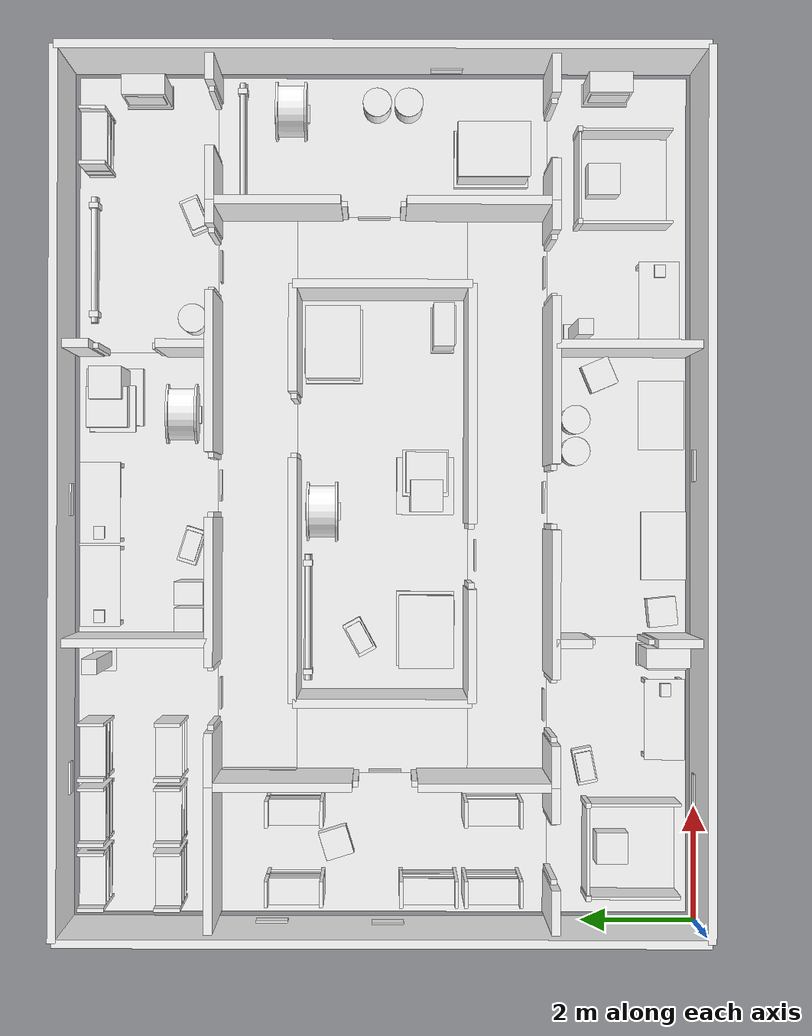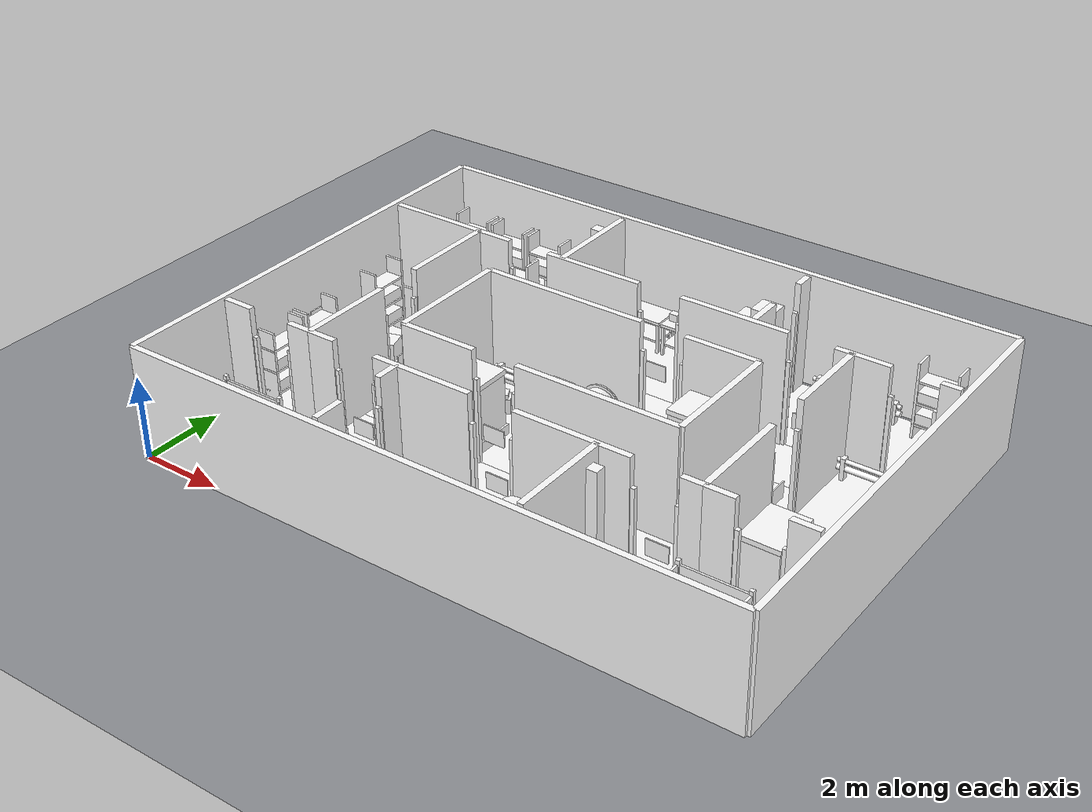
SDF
<?xml version="1.0"?>
<!-- Hexapod industrial robotics facility: an RGB-D SLAM benchmark world.
     Generated by hexapod_worlds/generate.py - edit layout.py / textures.py. -->
<sdf version="1.10">
  <world name="hexapod_facility">
    <physics name="1ms" type="ignored">
      <max_step_size>0.001</max_step_size>
      <real_time_factor>1.0</real_time_factor>
    </physics>
    <plugin filename="gz-sim-physics-system" name="gz::sim::systems::Physics"/>
    <plugin filename="gz-sim-user-commands-system" name="gz::sim::systems::UserCommands"/>
    <plugin filename="gz-sim-scene-broadcaster-system" name="gz::sim::systems::SceneBroadcaster"/>

    <scene>
      <ambient>0.5 0.5 0.53 1</ambient>
      <background>0.72 0.75 0.80 1</background>
      <grid>false</grid>
      <!-- shadows off: they cost more than they add for a
           camera 0.14 m off the floor, and RGB-D rendering is the budget -->
      <shadows>false</shadows>
    </scene>

    <light type="directional" name="sun">
      <pose>0 0 12 0 0 0</pose>
      <direction>-0.4 0.35 -0.9</direction>
      <diffuse>0.85 0.85 0.83 1</diffuse>
      <specular>0.15 0.15 0.15 1</specular>
      <cast_shadows>false</cast_shadows>
    </light>
    <light type="point" name="lamp_ring_w">
      <pose>3.3 5.5 2.5 0 0 0</pose>
      <diffuse>0.96 0.96 0.98 1</diffuse>
      <specular>0.15 0.15 0.15 1</specular>
      <attenuation><range>9</range><constant>0.35</constant><linear>0.06</linear>
        <quadratic>0.006</quadratic></attenuation>
      <cast_shadows>false</cast_shadows>
    </light>
    <light type="point" name="lamp_ring_e">
      <pose>11.7 5.5 2.5 0 0 0</pose>
      <diffuse>0.96 0.96 0.98 1</diffuse>
      <specular>0.15 0.15 0.15 1</specular>
      <attenuation><range>9</range><constant>0.35</constant><linear>0.06</linear>
        <quadratic>0.006</quadratic></attenuation>
      <cast_shadows>false</cast_shadows>
    </light>
    <light type="point" name="lamp_core">
      <pose>7.5 5.5 2.5 0 0 0</pose>
      <diffuse>1.0 0.98 0.92 1</diffuse>
      <specular>0.15 0.15 0.15 1</specular>
      <attenuation><range>9</range><constant>0.35</constant><linear>0.06</linear>
        <quadratic>0.006</quadratic></attenuation>
      <cast_shadows>false</cast_shadows>
    </light>
    <light type="point" name="lamp_south">
      <pose>7.5 1.4 2.5 0 0 0</pose>
      <diffuse>1.0 0.94 0.84 1</diffuse>
      <specular>0.15 0.15 0.15 1</specular>
      <attenuation><range>9</range><constant>0.35</constant><linear>0.06</linear>
        <quadratic>0.006</quadratic></attenuation>
      <cast_shadows>false</cast_shadows>
    </light>
    <light type="point" name="lamp_north">
      <pose>7.5 9.6 2.5 0 0 0</pose>
      <diffuse>0.94 0.98 1.0 1</diffuse>
      <specular>0.15 0.15 0.15 1</specular>
      <attenuation><range>9</range><constant>0.35</constant><linear>0.06</linear>
        <quadratic>0.006</quadratic></attenuation>
      <cast_shadows>false</cast_shadows>
    </light>
    <light type="point" name="lamp_west">
      <pose>1.4 5.5 2.4 0 0 0</pose>
      <diffuse>0.95 0.95 0.95 1</diffuse>
      <specular>0.15 0.15 0.15 1</specular>
      <attenuation><range>9</range><constant>0.35</constant><linear>0.06</linear>
        <quadratic>0.006</quadratic></attenuation>
      <cast_shadows>false</cast_shadows>
    </light>
    <light type="point" name="lamp_east">
      <pose>13.6 5.5 2.4 0 0 0</pose>
      <diffuse>0.98 0.96 0.9 1</diffuse>
      <specular>0.15 0.15 0.15 1</specular>
      <attenuation><range>9</range><constant>0.35</constant><linear>0.06</linear>
        <quadratic>0.006</quadratic></attenuation>
      <cast_shadows>false</cast_shadows>
    </light>
    <light type="point" name="lamp_southeast">
      <pose>12.4 1.4 2.5 0 0 0</pose>
      <diffuse>0.96 1.0 0.94 1</diffuse>
      <specular>0.15 0.15 0.15 1</specular>
      <attenuation><range>9</range><constant>0.35</constant><linear>0.06</linear>
        <quadratic>0.006</quadratic></attenuation>
      <cast_shadows>false</cast_shadows>
    </light>
    <light type="point" name="lamp_southwest">
      <pose>2.4 1.4 2.5 0 0 0</pose>
      <diffuse>0.92 0.96 1.0 1</diffuse>
      <specular>0.15 0.15 0.15 1</specular>
      <attenuation><range>9</range><constant>0.35</constant><linear>0.06</linear>
        <quadratic>0.006</quadratic></attenuation>
      <cast_shadows>false</cast_shadows>
    </light>

    <model name="ground">
      <static>true</static>
      <link name="plane">
        <visual name="vis">
          <geometry><plane><normal>0 0 1</normal><size>60 60</size></plane></geometry>
          <material><diffuse>0.55 0.56 0.58 1</diffuse></material>
        </visual>
      </link>
    </model>
    <model name="floors">
      <static>true</static>
      <link name="slabs">
        <collision name="floor_ring_0_col"><pose>7.500 3.300 -0.02 0 0 0</pose>
          <geometry><box><size>9.800 1.400 0.04</size></box></geometry>
          <surface><friction><ode><mu>1.0</mu><mu2>1.0</mu2></ode></friction></surface></collision>
        <visual name="floor_ring_0_vis"><pose>7.500 3.300 -0.02 0 0 0</pose>
          <geometry><box><size>9.800 1.400 0.04</size></box></geometry>
          <material>
          <diffuse>1 1 1 1</diffuse>
          <specular>0.15 0.15 0.15 1</specular>
          <pbr><metal>
            <albedo_map>model://slam_assets/materials/textures/floor_lane.png</albedo_map>
            <roughness>0.85</roughness><metalness>0.0</metalness>
          </metal></pbr>
        </material>
        </visual>
        <collision name="floor_ring_1_col"><pose>7.500 7.700 -0.02 0 0 0</pose>
          <geometry><box><size>9.800 1.400 0.04</size></box></geometry>
          <surface><friction><ode><mu>1.0</mu><mu2>1.0</mu2></ode></friction></surface></collision>
        <visual name="floor_ring_1_vis"><pose>7.500 7.700 -0.02 0 0 0</pose>
          <geometry><box><size>9.800 1.400 0.04</size></box></geometry>
          <material>
          <diffuse>1 1 1 1</diffuse>
          <specular>0.15 0.15 0.15 1</specular>
          <pbr><metal>
            <albedo_map>model://slam_assets/materials/textures/floor_lane.png</albedo_map>
            <roughness>0.85</roughness><metalness>0.0</metalness>
          </metal></pbr>
        </material>
        </visual>
        <collision name="floor_ring_2_col"><pose>3.300 5.500 -0.02 0 0 0</pose>
          <geometry><box><size>1.400 3.000 0.04</size></box></geometry>
          <surface><friction><ode><mu>1.0</mu><mu2>1.0</mu2></ode></friction></surface></collision>
        <visual name="floor_ring_2_vis"><pose>3.300 5.500 -0.02 0 0 0</pose>
          <geometry><box><size>1.400 3.000 0.04</size></box></geometry>
          <material>
          <diffuse>1 1 1 1</diffuse>
          <specular>0.15 0.15 0.15 1</specular>
          <pbr><metal>
            <albedo_map>model://slam_assets/materials/textures/floor_lane.png</albedo_map>
            <roughness>0.85</roughness><metalness>0.0</metalness>
          </metal></pbr>
        </material>
        </visual>
        <collision name="floor_ring_3_col"><pose>11.700 5.500 -0.02 0 0 0</pose>
          <geometry><box><size>1.400 3.000 0.04</size></box></geometry>
          <surface><friction><ode><mu>1.0</mu><mu2>1.0</mu2></ode></friction></surface></collision>
        <visual name="floor_ring_3_vis"><pose>11.700 5.500 -0.02 0 0 0</pose>
          <geometry><box><size>1.400 3.000 0.04</size></box></geometry>
          <material>
          <diffuse>1 1 1 1</diffuse>
          <specular>0.15 0.15 0.15 1</specular>
          <pbr><metal>
            <albedo_map>model://slam_assets/materials/textures/floor_lane.png</albedo_map>
            <roughness>0.85</roughness><metalness>0.0</metalness>
          </metal></pbr>
        </material>
        </visual>
        <collision name="floor_core_4_col"><pose>7.500 5.500 -0.02 0 0 0</pose>
          <geometry><box><size>7.000 3.000 0.04</size></box></geometry>
          <surface><friction><ode><mu>1.0</mu><mu2>1.0</mu2></ode></friction></surface></collision>
        <visual name="floor_core_4_vis"><pose>7.500 5.500 -0.02 0 0 0</pose>
          <geometry><box><size>7.000 3.000 0.04</size></box></geometry>
          <material>
          <diffuse>1 1 1 1</diffuse>
          <specular>0.15 0.15 0.15 1</specular>
          <pbr><metal>
            <albedo_map>model://slam_assets/materials/textures/floor_checkerplate.png</albedo_map>
            <roughness>0.85</roughness><metalness>0.0</metalness>
          </metal></pbr>
        </material>
        </visual>
        <collision name="floor_lab_5_col"><pose>2.575 1.375 -0.02 0 0 0</pose>
          <geometry><box><size>4.850 2.450 0.04</size></box></geometry>
          <surface><friction><ode><mu>1.0</mu><mu2>1.0</mu2></ode></friction></surface></collision>
        <visual name="floor_lab_5_vis"><pose>2.575 1.375 -0.02 0 0 0</pose>
          <geometry><box><size>4.850 2.450 0.04</size></box></geometry>
          <material>
          <diffuse>1 1 1 1</diffuse>
          <specular>0.15 0.15 0.15 1</specular>
          <pbr><metal>
            <albedo_map>model://slam_assets/materials/textures/floor_esd.png</albedo_map>
            <roughness>0.85</roughness><metalness>0.0</metalness>
          </metal></pbr>
        </material>
        </visual>
        <collision name="floor_loading_6_col"><pose>7.500 1.375 -0.02 0 0 0</pose>
          <geometry><box><size>5.000 2.450 0.04</size></box></geometry>
          <surface><friction><ode><mu>1.0</mu><mu2>1.0</mu2></ode></friction></surface></collision>
        <visual name="floor_loading_6_vis"><pose>7.500 1.375 -0.02 0 0 0</pose>
          <geometry><box><size>5.000 2.450 0.04</size></box></geometry>
          <material>
          <diffuse>1 1 1 1</diffuse>
          <specular>0.15 0.15 0.15 1</specular>
          <pbr><metal>
            <albedo_map>model://slam_assets/materials/textures/floor_hazard.png</albedo_map>
            <roughness>0.85</roughness><metalness>0.0</metalness>
          </metal></pbr>
        </material>
        </visual>
        <collision name="floor_testing_7_col"><pose>12.425 1.375 -0.02 0 0 0</pose>
          <geometry><box><size>4.850 2.450 0.04</size></box></geometry>
          <surface><friction><ode><mu>1.0</mu><mu2>1.0</mu2></ode></friction></surface></collision>
        <visual name="floor_testing_7_vis"><pose>12.425 1.375 -0.02 0 0 0</pose>
          <geometry><box><size>4.850 2.450 0.04</size></box></geometry>
          <material>
          <diffuse>1 1 1 1</diffuse>
          <specular>0.15 0.15 0.15 1</specular>
          <pbr><metal>
            <albedo_map>model://slam_assets/materials/textures/floor_epoxy_green.png</albedo_map>
            <roughness>0.85</roughness><metalness>0.0</metalness>
          </metal></pbr>
        </material>
        </visual>
        <collision name="floor_storage_8_col"><pose>2.575 9.625 -0.02 0 0 0</pose>
          <geometry><box><size>4.850 2.450 0.04</size></box></geometry>
          <surface><friction><ode><mu>1.0</mu><mu2>1.0</mu2></ode></friction></surface></collision>
        <visual name="floor_storage_8_vis"><pose>2.575 9.625 -0.02 0 0 0</pose>
          <geometry><box><size>4.850 2.450 0.04</size></box></geometry>
          <material>
          <diffuse>1 1 1 1</diffuse>
          <specular>0.15 0.15 0.15 1</specular>
          <pbr><metal>
            <albedo_map>model://slam_assets/materials/textures/floor_concrete.png</albedo_map>
            <roughness>0.85</roughness><metalness>0.0</metalness>
          </metal></pbr>
        </material>
        </visual>
        <collision name="floor_workshop_9_col"><pose>7.500 9.625 -0.02 0 0 0</pose>
          <geometry><box><size>5.000 2.450 0.04</size></box></geometry>
          <surface><friction><ode><mu>1.0</mu><mu2>1.0</mu2></ode></friction></surface></collision>
        <visual name="floor_workshop_9_vis"><pose>7.500 9.625 -0.02 0 0 0</pose>
          <geometry><box><size>5.000 2.450 0.04</size></box></geometry>
          <material>
          <diffuse>1 1 1 1</diffuse>
          <specular>0.15 0.15 0.15 1</specular>
          <pbr><metal>
            <albedo_map>model://slam_assets/materials/textures/floor_concrete_oil.png</albedo_map>
            <roughness>0.85</roughness><metalness>0.0</metalness>
          </metal></pbr>
        </material>
        </visual>
        <collision name="floor_maintenance_10_col"><pose>12.425 9.625 -0.02 0 0 0</pose>
          <geometry><box><size>4.850 2.450 0.04</size></box></geometry>
          <surface><friction><ode><mu>1.0</mu><mu2>1.0</mu2></ode></friction></surface></collision>
        <visual name="floor_maintenance_10_vis"><pose>12.425 9.625 -0.02 0 0 0</pose>
          <geometry><box><size>4.850 2.450 0.04</size></box></geometry>
          <material>
          <diffuse>1 1 1 1</diffuse>
          <specular>0.15 0.15 0.15 1</specular>
          <pbr><metal>
            <albedo_map>model://slam_assets/materials/textures/floor_steel_plate.png</albedo_map>
            <roughness>0.85</roughness><metalness>0.0</metalness>
          </metal></pbr>
        </material>
        </visual>
        <collision name="floor_parts_11_col"><pose>1.375 5.500 -0.02 0 0 0</pose>
          <geometry><box><size>2.450 5.800 0.04</size></box></geometry>
          <surface><friction><ode><mu>1.0</mu><mu2>1.0</mu2></ode></friction></surface></collision>
        <visual name="floor_parts_11_vis"><pose>1.375 5.500 -0.02 0 0 0</pose>
          <geometry><box><size>2.450 5.800 0.04</size></box></geometry>
          <material>
          <diffuse>1 1 1 1</diffuse>
          <specular>0.15 0.15 0.15 1</specular>
          <pbr><metal>
            <albedo_map>model://slam_assets/materials/textures/floor_tile_grey.png</albedo_map>
            <roughness>0.85</roughness><metalness>0.0</metalness>
          </metal></pbr>
        </material>
        </visual>
        <collision name="floor_equipment_12_col"><pose>13.625 5.500 -0.02 0 0 0</pose>
          <geometry><box><size>2.450 5.800 0.04</size></box></geometry>
          <surface><friction><ode><mu>1.0</mu><mu2>1.0</mu2></ode></friction></surface></collision>
        <visual name="floor_equipment_12_vis"><pose>13.625 5.500 -0.02 0 0 0</pose>
          <geometry><box><size>2.450 5.800 0.04</size></box></geometry>
          <material>
          <diffuse>1 1 1 1</diffuse>
          <specular>0.15 0.15 0.15 1</specular>
          <pbr><metal>
            <albedo_map>model://slam_assets/materials/textures/floor_concrete.png</albedo_map>
            <roughness>0.85</roughness><metalness>0.0</metalness>
          </metal></pbr>
        </material>
        </visual>
      </link>
    </model>
    <model name="building">
      <static>true</static>
      <link name="structure">
        <collision name="wall_0_col"><pose>7.500 0.000 1.400 0 0 0</pose>
          <geometry><box><size>15.000 0.15 2.8</size></box></geometry></collision>
        <visual name="wall_0_vis"><pose>7.500 0.000 1.400 0 0 0</pose>
          <geometry><box><size>15.000 0.15 2.8</size></box></geometry>
          <material>
          <diffuse>1 1 1 1</diffuse>
          <specular>0.15 0.15 0.15 1</specular>
          <pbr><metal>
            <albedo_map>model://slam_assets/materials/textures/wall_loading.png</albedo_map>
            <roughness>0.85</roughness><metalness>0.0</metalness>
          </metal></pbr>
        </material>
        </visual>
        <collision name="wall_1_col"><pose>7.500 11.000 1.400 0 0 0</pose>
          <geometry><box><size>15.000 0.15 2.8</size></box></geometry></collision>
        <visual name="wall_1_vis"><pose>7.500 11.000 1.400 0 0 0</pose>
          <geometry><box><size>15.000 0.15 2.8</size></box></geometry>
          <material>
          <diffuse>1 1 1 1</diffuse>
          <specular>0.15 0.15 0.15 1</specular>
          <pbr><metal>
            <albedo_map>model://slam_assets/materials/textures/wall_workshop.png</albedo_map>
            <roughness>0.85</roughness><metalness>0.0</metalness>
          </metal></pbr>
        </material>
        </visual>
        <collision name="wall_2_col"><pose>0.000 5.500 1.400 0 0 0</pose>
          <geometry><box><size>0.15 11.000 2.8</size></box></geometry></collision>
        <visual name="wall_2_vis"><pose>0.000 5.500 1.400 0 0 0</pose>
          <geometry><box><size>0.15 11.000 2.8</size></box></geometry>
          <material>
          <diffuse>1 1 1 1</diffuse>
          <specular>0.15 0.15 0.15 1</specular>
          <pbr><metal>
            <albedo_map>model://slam_assets/materials/textures/wall_parts.png</albedo_map>
            <roughness>0.85</roughness><metalness>0.0</metalness>
          </metal></pbr>
        </material>
        </visual>
        <collision name="wall_3_col"><pose>15.000 5.500 1.400 0 0 0</pose>
          <geometry><box><size>0.15 11.000 2.8</size></box></geometry></collision>
        <visual name="wall_3_vis"><pose>15.000 5.500 1.400 0 0 0</pose>
          <geometry><box><size>0.15 11.000 2.8</size></box></geometry>
          <material>
          <diffuse>1 1 1 1</diffuse>
          <specular>0.15 0.15 0.15 1</specular>
          <pbr><metal>
            <albedo_map>model://slam_assets/materials/textures/wall_equipment.png</albedo_map>
            <roughness>0.85</roughness><metalness>0.0</metalness>
          </metal></pbr>
        </material>
        </visual>
        <collision name="wall_4_col"><pose>2.950 2.600 1.400 0 0 0</pose>
          <geometry><box><size>0.700 0.15 2.8</size></box></geometry></collision>
        <visual name="wall_4_vis"><pose>2.950 2.600 1.400 0 0 0</pose>
          <geometry><box><size>0.700 0.15 2.8</size></box></geometry>
          <material>
          <diffuse>1 1 1 1</diffuse>
          <specular>0.15 0.15 0.15 1</specular>
          <pbr><metal>
            <albedo_map>model://slam_assets/materials/textures/wall_lab.png</albedo_map>
            <roughness>0.85</roughness><metalness>0.0</metalness>
          </metal></pbr>
        </material>
        </visual>
        <collision name="wall_5_col"><pose>5.650 2.600 1.400 0 0 0</pose>
          <geometry><box><size>2.500 0.15 2.8</size></box></geometry></collision>
        <visual name="wall_5_vis"><pose>5.650 2.600 1.400 0 0 0</pose>
          <geometry><box><size>2.500 0.15 2.8</size></box></geometry>
          <material>
          <diffuse>1 1 1 1</diffuse>
          <specular>0.15 0.15 0.15 1</specular>
          <pbr><metal>
            <albedo_map>model://slam_assets/materials/textures/wall_loading.png</albedo_map>
            <roughness>0.85</roughness><metalness>0.0</metalness>
          </metal></pbr>
        </material>
        </visual>
        <collision name="wall_6_col"><pose>9.400 2.600 1.400 0 0 0</pose>
          <geometry><box><size>2.800 0.15 2.8</size></box></geometry></collision>
        <visual name="wall_6_vis"><pose>9.400 2.600 1.400 0 0 0</pose>
          <geometry><box><size>2.800 0.15 2.8</size></box></geometry>
          <material>
          <diffuse>1 1 1 1</diffuse>
          <specular>0.15 0.15 0.15 1</specular>
          <pbr><metal>
            <albedo_map>model://slam_assets/materials/textures/wall_loading.png</albedo_map>
            <roughness>0.85</roughness><metalness>0.0</metalness>
          </metal></pbr>
        </material>
        </visual>
        <collision name="wall_7_col"><pose>12.150 2.600 1.400 0 0 0</pose>
          <geometry><box><size>0.500 0.15 2.8</size></box></geometry></collision>
        <visual name="wall_7_vis"><pose>12.150 2.600 1.400 0 0 0</pose>
          <geometry><box><size>0.500 0.15 2.8</size></box></geometry>
          <material>
          <diffuse>1 1 1 1</diffuse>
          <specular>0.15 0.15 0.15 1</specular>
          <pbr><metal>
            <albedo_map>model://slam_assets/materials/textures/wall_testing.png</albedo_map>
            <roughness>0.85</roughness><metalness>0.0</metalness>
          </metal></pbr>
        </material>
        </visual>
        <collision name="wall_8_col"><pose>3.050 8.400 1.400 0 0 0</pose>
          <geometry><box><size>0.900 0.15 2.8</size></box></geometry></collision>
        <visual name="wall_8_vis"><pose>3.050 8.400 1.400 0 0 0</pose>
          <geometry><box><size>0.900 0.15 2.8</size></box></geometry>
          <material>
          <diffuse>1 1 1 1</diffuse>
          <specular>0.15 0.15 0.15 1</specular>
          <pbr><metal>
            <albedo_map>model://slam_assets/materials/textures/wall_storage.png</albedo_map>
            <roughness>0.85</roughness><metalness>0.0</metalness>
          </metal></pbr>
        </material>
        </visual>
        <collision name="wall_9_col"><pose>5.850 8.400 1.400 0 0 0</pose>
          <geometry><box><size>2.500 0.15 2.8</size></box></geometry></collision>
        <visual name="wall_9_vis"><pose>5.850 8.400 1.400 0 0 0</pose>
          <geometry><box><size>2.500 0.15 2.8</size></box></geometry>
          <material>
          <diffuse>1 1 1 1</diffuse>
          <specular>0.15 0.15 0.15 1</specular>
          <pbr><metal>
            <albedo_map>model://slam_assets/materials/textures/wall_workshop.png</albedo_map>
            <roughness>0.85</roughness><metalness>0.0</metalness>
          </metal></pbr>
        </material>
        </visual>
        <collision name="wall_10_col"><pose>9.550 8.400 1.400 0 0 0</pose>
          <geometry><box><size>2.700 0.15 2.8</size></box></geometry></collision>
        <visual name="wall_10_vis"><pose>9.550 8.400 1.400 0 0 0</pose>
          <geometry><box><size>2.700 0.15 2.8</size></box></geometry>
          <material>
          <diffuse>1 1 1 1</diffuse>
          <specular>0.15 0.15 0.15 1</specular>
          <pbr><metal>
            <albedo_map>model://slam_assets/materials/textures/wall_workshop.png</albedo_map>
            <roughness>0.85</roughness><metalness>0.0</metalness>
          </metal></pbr>
        </material>
        </visual>
        <collision name="wall_11_col"><pose>12.200 8.400 1.400 0 0 0</pose>
          <geometry><box><size>0.400 0.15 2.8</size></box></geometry></collision>
        <visual name="wall_11_vis"><pose>12.200 8.400 1.400 0 0 0</pose>
          <geometry><box><size>0.400 0.15 2.8</size></box></geometry>
          <material>
          <diffuse>1 1 1 1</diffuse>
          <specular>0.15 0.15 0.15 1</specular>
          <pbr><metal>
            <albedo_map>model://slam_assets/materials/textures/wall_maintenance.png</albedo_map>
            <roughness>0.85</roughness><metalness>0.0</metalness>
          </metal></pbr>
        </material>
        </visual>
        <collision name="wall_12_col"><pose>2.600 3.750 1.400 0 0 0</pose>
          <geometry><box><size>0.15 2.300 2.8</size></box></geometry></collision>
        <visual name="wall_12_vis"><pose>2.600 3.750 1.400 0 0 0</pose>
          <geometry><box><size>0.15 2.300 2.8</size></box></geometry>
          <material>
          <diffuse>1 1 1 1</diffuse>
          <specular>0.15 0.15 0.15 1</specular>
          <pbr><metal>
            <albedo_map>model://slam_assets/materials/textures/wall_parts.png</albedo_map>
            <roughness>0.85</roughness><metalness>0.0</metalness>
          </metal></pbr>
        </material>
        </visual>
        <collision name="wall_13_col"><pose>2.600 7.200 1.400 0 0 0</pose>
          <geometry><box><size>0.15 2.400 2.8</size></box></geometry></collision>
        <visual name="wall_13_vis"><pose>2.600 7.200 1.400 0 0 0</pose>
          <geometry><box><size>0.15 2.400 2.8</size></box></geometry>
          <material>
          <diffuse>1 1 1 1</diffuse>
          <specular>0.15 0.15 0.15 1</specular>
          <pbr><metal>
            <albedo_map>model://slam_assets/materials/textures/wall_parts.png</albedo_map>
            <roughness>0.85</roughness><metalness>0.0</metalness>
          </metal></pbr>
        </material>
        </visual>
        <collision name="wall_14_col"><pose>12.400 3.850 1.400 0 0 0</pose>
          <geometry><box><size>0.15 2.500 2.8</size></box></geometry></collision>
        <visual name="wall_14_vis"><pose>12.400 3.850 1.400 0 0 0</pose>
          <geometry><box><size>0.15 2.500 2.8</size></box></geometry>
          <material>
          <diffuse>1 1 1 1</diffuse>
          <specular>0.15 0.15 0.15 1</specular>
          <pbr><metal>
            <albedo_map>model://slam_assets/materials/textures/wall_equipment.png</albedo_map>
            <roughness>0.85</roughness><metalness>0.0</metalness>
          </metal></pbr>
        </material>
        </visual>
        <collision name="wall_15_col"><pose>12.400 7.300 1.400 0 0 0</pose>
          <geometry><box><size>0.15 2.200 2.8</size></box></geometry></collision>
        <visual name="wall_15_vis"><pose>12.400 7.300 1.400 0 0 0</pose>
          <geometry><box><size>0.15 2.200 2.8</size></box></geometry>
          <material>
          <diffuse>1 1 1 1</diffuse>
          <specular>0.15 0.15 0.15 1</specular>
          <pbr><metal>
            <albedo_map>model://slam_assets/materials/textures/wall_equipment.png</albedo_map>
            <roughness>0.85</roughness><metalness>0.0</metalness>
          </metal></pbr>
        </material>
        </visual>
        <collision name="wall_16_col"><pose>4.950 4.000 1.400 0 0 0</pose>
          <geometry><box><size>1.900 0.15 2.8</size></box></geometry></collision>
        <visual name="wall_16_vis"><pose>4.950 4.000 1.400 0 0 0</pose>
          <geometry><box><size>1.900 0.15 2.8</size></box></geometry>
          <material>
          <diffuse>1 1 1 1</diffuse>
          <specular>0.15 0.15 0.15 1</specular>
          <pbr><metal>
            <albedo_map>model://slam_assets/materials/textures/wall_machine.png</albedo_map>
            <roughness>0.85</roughness><metalness>0.0</metalness>
          </metal></pbr>
        </material>
        </visual>
        <collision name="wall_17_col"><pose>9.000 4.000 1.400 0 0 0</pose>
          <geometry><box><size>4.000 0.15 2.8</size></box></geometry></collision>
        <visual name="wall_17_vis"><pose>9.000 4.000 1.400 0 0 0</pose>
          <geometry><box><size>4.000 0.15 2.8</size></box></geometry>
          <material>
          <diffuse>1 1 1 1</diffuse>
          <specular>0.15 0.15 0.15 1</specular>
          <pbr><metal>
            <albedo_map>model://slam_assets/materials/textures/wall_machine.png</albedo_map>
            <roughness>0.85</roughness><metalness>0.0</metalness>
          </metal></pbr>
        </material>
        </visual>
        <collision name="wall_18_col"><pose>6.050 7.000 1.400 0 0 0</pose>
          <geometry><box><size>4.100 0.15 2.8</size></box></geometry></collision>
        <visual name="wall_18_vis"><pose>6.050 7.000 1.400 0 0 0</pose>
          <geometry><box><size>4.100 0.15 2.8</size></box></geometry>
          <material>
          <diffuse>1 1 1 1</diffuse>
          <specular>0.15 0.15 0.15 1</specular>
          <pbr><metal>
            <albedo_map>model://slam_assets/materials/textures/wall_machine.png</albedo_map>
            <roughness>0.85</roughness><metalness>0.0</metalness>
          </metal></pbr>
        </material>
        </visual>
        <collision name="wall_19_col"><pose>10.100 7.000 1.400 0 0 0</pose>
          <geometry><box><size>1.800 0.15 2.8</size></box></geometry></collision>
        <visual name="wall_19_vis"><pose>10.100 7.000 1.400 0 0 0</pose>
          <geometry><box><size>1.800 0.15 2.8</size></box></geometry>
          <material>
          <diffuse>1 1 1 1</diffuse>
          <specular>0.15 0.15 0.15 1</specular>
          <pbr><metal>
            <albedo_map>model://slam_assets/materials/textures/wall_machine.png</albedo_map>
            <roughness>0.85</roughness><metalness>0.0</metalness>
          </metal></pbr>
        </material>
        </visual>
        <collision name="wall_20_col"><pose>4.000 5.500 1.400 0 0 0</pose>
          <geometry><box><size>0.15 3.000 2.8</size></box></geometry></collision>
        <visual name="wall_20_vis"><pose>4.000 5.500 1.400 0 0 0</pose>
          <geometry><box><size>0.15 3.000 2.8</size></box></geometry>
          <material>
          <diffuse>1 1 1 1</diffuse>
          <specular>0.15 0.15 0.15 1</specular>
          <pbr><metal>
            <albedo_map>model://slam_assets/materials/textures/wall_machine.png</albedo_map>
            <roughness>0.85</roughness><metalness>0.0</metalness>
          </metal></pbr>
        </material>
        </visual>
        <collision name="wall_21_col"><pose>11.000 5.500 1.400 0 0 0</pose>
          <geometry><box><size>0.15 3.000 2.8</size></box></geometry></collision>
        <visual name="wall_21_vis"><pose>11.000 5.500 1.400 0 0 0</pose>
          <geometry><box><size>0.15 3.000 2.8</size></box></geometry>
          <material>
          <diffuse>1 1 1 1</diffuse>
          <specular>0.15 0.15 0.15 1</specular>
          <pbr><metal>
            <albedo_map>model://slam_assets/materials/textures/wall_machine.png</albedo_map>
            <roughness>0.85</roughness><metalness>0.0</metalness>
          </metal></pbr>
        </material>
        </visual>
        <collision name="wall_22_col"><pose>5.000 0.525 1.400 0 0 0</pose>
          <geometry><box><size>0.15 0.750 2.8</size></box></geometry></collision>
        <visual name="wall_22_vis"><pose>5.000 0.525 1.400 0 0 0</pose>
          <geometry><box><size>0.15 0.750 2.8</size></box></geometry>
          <material>
          <diffuse>1 1 1 1</diffuse>
          <specular>0.15 0.15 0.15 1</specular>
          <pbr><metal>
            <albedo_map>model://slam_assets/materials/textures/wall_lab.png</albedo_map>
            <roughness>0.85</roughness><metalness>0.0</metalness>
          </metal></pbr>
        </material>
        </visual>
        <collision name="wall_23_col"><pose>5.000 2.300 1.400 0 0 0</pose>
          <geometry><box><size>0.15 0.600 2.8</size></box></geometry></collision>
        <visual name="wall_23_vis"><pose>5.000 2.300 1.400 0 0 0</pose>
          <geometry><box><size>0.15 0.600 2.8</size></box></geometry>
          <material>
          <diffuse>1 1 1 1</diffuse>
          <specular>0.15 0.15 0.15 1</specular>
          <pbr><metal>
            <albedo_map>model://slam_assets/materials/textures/wall_lab.png</albedo_map>
            <roughness>0.85</roughness><metalness>0.0</metalness>
          </metal></pbr>
        </material>
        </visual>
        <collision name="wall_24_col"><pose>10.000 1.375 1.400 0 0 0</pose>
          <geometry><box><size>0.15 2.450 2.8</size></box></geometry></collision>
        <visual name="wall_24_vis"><pose>10.000 1.375 1.400 0 0 0</pose>
          <geometry><box><size>0.15 2.450 2.8</size></box></geometry>
          <material>
          <diffuse>1 1 1 1</diffuse>
          <specular>0.15 0.15 0.15 1</specular>
          <pbr><metal>
            <albedo_map>model://slam_assets/materials/textures/wall_loading.png</albedo_map>
            <roughness>0.85</roughness><metalness>0.0</metalness>
          </metal></pbr>
        </material>
        </visual>
        <collision name="wall_25_col"><pose>5.000 9.625 1.400 0 0 0</pose>
          <geometry><box><size>0.15 2.450 2.8</size></box></geometry></collision>
        <visual name="wall_25_vis"><pose>5.000 9.625 1.400 0 0 0</pose>
          <geometry><box><size>0.15 2.450 2.8</size></box></geometry>
          <material>
          <diffuse>1 1 1 1</diffuse>
          <specular>0.15 0.15 0.15 1</specular>
          <pbr><metal>
            <albedo_map>model://slam_assets/materials/textures/wall_storage.png</albedo_map>
            <roughness>0.85</roughness><metalness>0.0</metalness>
          </metal></pbr>
        </material>
        </visual>
        <collision name="wall_26_col"><pose>10.000 8.850 1.400 0 0 0</pose>
          <geometry><box><size>0.15 0.900 2.8</size></box></geometry></collision>
        <visual name="wall_26_vis"><pose>10.000 8.850 1.400 0 0 0</pose>
          <geometry><box><size>0.15 0.900 2.8</size></box></geometry>
          <material>
          <diffuse>1 1 1 1</diffuse>
          <specular>0.15 0.15 0.15 1</specular>
          <pbr><metal>
            <albedo_map>model://slam_assets/materials/textures/wall_workshop.png</albedo_map>
            <roughness>0.85</roughness><metalness>0.0</metalness>
          </metal></pbr>
        </material>
        </visual>
        <collision name="wall_27_col"><pose>10.000 10.625 1.400 0 0 0</pose>
          <geometry><box><size>0.15 0.450 2.8</size></box></geometry></collision>
        <visual name="wall_27_vis"><pose>10.000 10.625 1.400 0 0 0</pose>
          <geometry><box><size>0.15 0.450 2.8</size></box></geometry>
          <material>
          <diffuse>1 1 1 1</diffuse>
          <specular>0.15 0.15 0.15 1</specular>
          <pbr><metal>
            <albedo_map>model://slam_assets/materials/textures/wall_workshop.png</albedo_map>
            <roughness>0.85</roughness><metalness>0.0</metalness>
          </metal></pbr>
        </material>
        </visual>
        <collision name="wall_28_col"><pose>0.525 2.600 1.400 0 0 0</pose>
          <geometry><box><size>0.750 0.15 2.8</size></box></geometry></collision>
        <visual name="wall_28_vis"><pose>0.525 2.600 1.400 0 0 0</pose>
          <geometry><box><size>0.750 0.15 2.8</size></box></geometry>
          <material>
          <diffuse>1 1 1 1</diffuse>
          <specular>0.15 0.15 0.15 1</specular>
          <pbr><metal>
            <albedo_map>model://slam_assets/materials/textures/wall_lab.png</albedo_map>
            <roughness>0.85</roughness><metalness>0.0</metalness>
          </metal></pbr>
        </material>
        </visual>
        <collision name="wall_29_col"><pose>2.300 2.600 1.400 0 0 0</pose>
          <geometry><box><size>0.600 0.15 2.8</size></box></geometry></collision>
        <visual name="wall_29_vis"><pose>2.300 2.600 1.400 0 0 0</pose>
          <geometry><box><size>0.600 0.15 2.8</size></box></geometry>
          <material>
          <diffuse>1 1 1 1</diffuse>
          <specular>0.15 0.15 0.15 1</specular>
          <pbr><metal>
            <albedo_map>model://slam_assets/materials/textures/wall_lab.png</albedo_map>
            <roughness>0.85</roughness><metalness>0.0</metalness>
          </metal></pbr>
        </material>
        </visual>
        <collision name="wall_30_col"><pose>1.375 8.400 1.400 0 0 0</pose>
          <geometry><box><size>2.450 0.15 2.8</size></box></geometry></collision>
        <visual name="wall_30_vis"><pose>1.375 8.400 1.400 0 0 0</pose>
          <geometry><box><size>2.450 0.15 2.8</size></box></geometry>
          <material>
          <diffuse>1 1 1 1</diffuse>
          <specular>0.15 0.15 0.15 1</specular>
          <pbr><metal>
            <albedo_map>model://slam_assets/materials/textures/wall_parts.png</albedo_map>
            <roughness>0.85</roughness><metalness>0.0</metalness>
          </metal></pbr>
        </material>
        </visual>
        <collision name="wall_31_col"><pose>12.750 2.600 1.400 0 0 0</pose>
          <geometry><box><size>0.700 0.15 2.8</size></box></geometry></collision>
        <visual name="wall_31_vis"><pose>12.750 2.600 1.400 0 0 0</pose>
          <geometry><box><size>0.700 0.15 2.8</size></box></geometry>
          <material>
          <diffuse>1 1 1 1</diffuse>
          <specular>0.15 0.15 0.15 1</specular>
          <pbr><metal>
            <albedo_map>model://slam_assets/materials/textures/wall_testing.png</albedo_map>
            <roughness>0.85</roughness><metalness>0.0</metalness>
          </metal></pbr>
        </material>
        </visual>
        <collision name="wall_32_col"><pose>14.525 2.600 1.400 0 0 0</pose>
          <geometry><box><size>0.650 0.15 2.8</size></box></geometry></collision>
        <visual name="wall_32_vis"><pose>14.525 2.600 1.400 0 0 0</pose>
          <geometry><box><size>0.650 0.15 2.8</size></box></geometry>
          <material>
          <diffuse>1 1 1 1</diffuse>
          <specular>0.15 0.15 0.15 1</specular>
          <pbr><metal>
            <albedo_map>model://slam_assets/materials/textures/wall_testing.png</albedo_map>
            <roughness>0.85</roughness><metalness>0.0</metalness>
          </metal></pbr>
        </material>
        </visual>
        <collision name="wall_33_col"><pose>12.850 8.400 1.400 0 0 0</pose>
          <geometry><box><size>0.900 0.15 2.8</size></box></geometry></collision>
        <visual name="wall_33_vis"><pose>12.850 8.400 1.400 0 0 0</pose>
          <geometry><box><size>0.900 0.15 2.8</size></box></geometry>
          <material>
          <diffuse>1 1 1 1</diffuse>
          <specular>0.15 0.15 0.15 1</specular>
          <pbr><metal>
            <albedo_map>model://slam_assets/materials/textures/wall_equipment.png</albedo_map>
            <roughness>0.85</roughness><metalness>0.0</metalness>
          </metal></pbr>
        </material>
        </visual>
        <collision name="wall_34_col"><pose>14.625 8.400 1.400 0 0 0</pose>
          <geometry><box><size>0.450 0.15 2.8</size></box></geometry></collision>
        <visual name="wall_34_vis"><pose>14.625 8.400 1.400 0 0 0</pose>
          <geometry><box><size>0.450 0.15 2.8</size></box></geometry>
          <material>
          <diffuse>1 1 1 1</diffuse>
          <specular>0.15 0.15 0.15 1</specular>
          <pbr><metal>
            <albedo_map>model://slam_assets/materials/textures/wall_equipment.png</albedo_map>
            <roughness>0.85</roughness><metalness>0.0</metalness>
          </metal></pbr>
        </material>
        </visual>
        <collision name="doorframe_0_col"><pose>3.300 2.600 1.05 0 0 0</pose>
          <geometry><box><size>0.19 0.10 2.10</size></box></geometry></collision>
        <visual name="doorframe_0_vis"><pose>3.300 2.600 1.05 0 0 0</pose>
          <geometry><box><size>0.19 0.10 2.10</size></box></geometry>
          <material>
          <diffuse>1 1 1 1</diffuse>
          <specular>0.15 0.15 0.15 1</specular>
          <pbr><metal>
            <albedo_map>model://slam_assets/materials/textures/pillar_paint.png</albedo_map>
            <roughness>0.85</roughness><metalness>0.0</metalness>
          </metal></pbr>
        </material>
        </visual>
        <collision name="doorframe_1_col"><pose>4.400 2.600 1.05 0 0 0</pose>
          <geometry><box><size>0.19 0.10 2.10</size></box></geometry></collision>
        <visual name="doorframe_1_vis"><pose>4.400 2.600 1.05 0 0 0</pose>
          <geometry><box><size>0.19 0.10 2.10</size></box></geometry>
          <material>
          <diffuse>1 1 1 1</diffuse>
          <specular>0.15 0.15 0.15 1</specular>
          <pbr><metal>
            <albedo_map>model://slam_assets/materials/textures/pillar_paint.png</albedo_map>
            <roughness>0.85</roughness><metalness>0.0</metalness>
          </metal></pbr>
        </material>
        </visual>
        <collision name="doorframe_2_col"><pose>6.900 2.600 1.05 0 0 0</pose>
          <geometry><box><size>0.19 0.10 2.10</size></box></geometry></collision>
        <visual name="doorframe_2_vis"><pose>6.900 2.600 1.05 0 0 0</pose>
          <geometry><box><size>0.19 0.10 2.10</size></box></geometry>
          <material>
          <diffuse>1 1 1 1</diffuse>
          <specular>0.15 0.15 0.15 1</specular>
          <pbr><metal>
            <albedo_map>model://slam_assets/materials/textures/pillar_paint.png</albedo_map>
            <roughness>0.85</roughness><metalness>0.0</metalness>
          </metal></pbr>
        </material>
        </visual>
        <collision name="doorframe_3_col"><pose>8.000 2.600 1.05 0 0 0</pose>
          <geometry><box><size>0.19 0.10 2.10</size></box></geometry></collision>
        <visual name="doorframe_3_vis"><pose>8.000 2.600 1.05 0 0 0</pose>
          <geometry><box><size>0.19 0.10 2.10</size></box></geometry>
          <material>
          <diffuse>1 1 1 1</diffuse>
          <specular>0.15 0.15 0.15 1</specular>
          <pbr><metal>
            <albedo_map>model://slam_assets/materials/textures/pillar_paint.png</albedo_map>
            <roughness>0.85</roughness><metalness>0.0</metalness>
          </metal></pbr>
        </material>
        </visual>
        <collision name="doorframe_4_col"><pose>10.800 2.600 1.05 0 0 0</pose>
          <geometry><box><size>0.19 0.10 2.10</size></box></geometry></collision>
        <visual name="doorframe_4_vis"><pose>10.800 2.600 1.05 0 0 0</pose>
          <geometry><box><size>0.19 0.10 2.10</size></box></geometry>
          <material>
          <diffuse>1 1 1 1</diffuse>
          <specular>0.15 0.15 0.15 1</specular>
          <pbr><metal>
            <albedo_map>model://slam_assets/materials/textures/pillar_paint.png</albedo_map>
            <roughness>0.85</roughness><metalness>0.0</metalness>
          </metal></pbr>
        </material>
        </visual>
        <collision name="doorframe_5_col"><pose>11.900 2.600 1.05 0 0 0</pose>
          <geometry><box><size>0.19 0.10 2.10</size></box></geometry></collision>
        <visual name="doorframe_5_vis"><pose>11.900 2.600 1.05 0 0 0</pose>
          <geometry><box><size>0.19 0.10 2.10</size></box></geometry>
          <material>
          <diffuse>1 1 1 1</diffuse>
          <specular>0.15 0.15 0.15 1</specular>
          <pbr><metal>
            <albedo_map>model://slam_assets/materials/textures/pillar_paint.png</albedo_map>
            <roughness>0.85</roughness><metalness>0.0</metalness>
          </metal></pbr>
        </material>
        </visual>
        <collision name="doorframe_6_col"><pose>3.500 8.400 1.05 0 0 0</pose>
          <geometry><box><size>0.19 0.10 2.10</size></box></geometry></collision>
        <visual name="doorframe_6_vis"><pose>3.500 8.400 1.05 0 0 0</pose>
          <geometry><box><size>0.19 0.10 2.10</size></box></geometry>
          <material>
          <diffuse>1 1 1 1</diffuse>
          <specular>0.15 0.15 0.15 1</specular>
          <pbr><metal>
            <albedo_map>model://slam_assets/materials/textures/pillar_paint.png</albedo_map>
            <roughness>0.85</roughness><metalness>0.0</metalness>
          </metal></pbr>
        </material>
        </visual>
        <collision name="doorframe_7_col"><pose>4.600 8.400 1.05 0 0 0</pose>
          <geometry><box><size>0.19 0.10 2.10</size></box></geometry></collision>
        <visual name="doorframe_7_vis"><pose>4.600 8.400 1.05 0 0 0</pose>
          <geometry><box><size>0.19 0.10 2.10</size></box></geometry>
          <material>
          <diffuse>1 1 1 1</diffuse>
          <specular>0.15 0.15 0.15 1</specular>
          <pbr><metal>
            <albedo_map>model://slam_assets/materials/textures/pillar_paint.png</albedo_map>
            <roughness>0.85</roughness><metalness>0.0</metalness>
          </metal></pbr>
        </material>
        </visual>
        <collision name="doorframe_8_col"><pose>7.100 8.400 1.05 0 0 0</pose>
          <geometry><box><size>0.19 0.10 2.10</size></box></geometry></collision>
        <visual name="doorframe_8_vis"><pose>7.100 8.400 1.05 0 0 0</pose>
          <geometry><box><size>0.19 0.10 2.10</size></box></geometry>
          <material>
          <diffuse>1 1 1 1</diffuse>
          <specular>0.15 0.15 0.15 1</specular>
          <pbr><metal>
            <albedo_map>model://slam_assets/materials/textures/pillar_paint.png</albedo_map>
            <roughness>0.85</roughness><metalness>0.0</metalness>
          </metal></pbr>
        </material>
        </visual>
        <collision name="doorframe_9_col"><pose>8.200 8.400 1.05 0 0 0</pose>
          <geometry><box><size>0.19 0.10 2.10</size></box></geometry></collision>
        <visual name="doorframe_9_vis"><pose>8.200 8.400 1.05 0 0 0</pose>
          <geometry><box><size>0.19 0.10 2.10</size></box></geometry>
          <material>
          <diffuse>1 1 1 1</diffuse>
          <specular>0.15 0.15 0.15 1</specular>
          <pbr><metal>
            <albedo_map>model://slam_assets/materials/textures/pillar_paint.png</albedo_map>
            <roughness>0.85</roughness><metalness>0.0</metalness>
          </metal></pbr>
        </material>
        </visual>
        <collision name="doorframe_10_col"><pose>10.900 8.400 1.05 0 0 0</pose>
          <geometry><box><size>0.19 0.10 2.10</size></box></geometry></collision>
        <visual name="doorframe_10_vis"><pose>10.900 8.400 1.05 0 0 0</pose>
          <geometry><box><size>0.19 0.10 2.10</size></box></geometry>
          <material>
          <diffuse>1 1 1 1</diffuse>
          <specular>0.15 0.15 0.15 1</specular>
          <pbr><metal>
            <albedo_map>model://slam_assets/materials/textures/pillar_paint.png</albedo_map>
            <roughness>0.85</roughness><metalness>0.0</metalness>
          </metal></pbr>
        </material>
        </visual>
        <collision name="doorframe_11_col"><pose>12.000 8.400 1.05 0 0 0</pose>
          <geometry><box><size>0.19 0.10 2.10</size></box></geometry></collision>
        <visual name="doorframe_11_vis"><pose>12.000 8.400 1.05 0 0 0</pose>
          <geometry><box><size>0.19 0.10 2.10</size></box></geometry>
          <material>
          <diffuse>1 1 1 1</diffuse>
          <specular>0.15 0.15 0.15 1</specular>
          <pbr><metal>
            <albedo_map>model://slam_assets/materials/textures/pillar_paint.png</albedo_map>
            <roughness>0.85</roughness><metalness>0.0</metalness>
          </metal></pbr>
        </material>
        </visual>
        <collision name="doorframe_12_col"><pose>2.600 4.900 1.05 0 0 0</pose>
          <geometry><box><size>0.10 0.19 2.10</size></box></geometry></collision>
        <visual name="doorframe_12_vis"><pose>2.600 4.900 1.05 0 0 0</pose>
          <geometry><box><size>0.10 0.19 2.10</size></box></geometry>
          <material>
          <diffuse>1 1 1 1</diffuse>
          <specular>0.15 0.15 0.15 1</specular>
          <pbr><metal>
            <albedo_map>model://slam_assets/materials/textures/pillar_paint.png</albedo_map>
            <roughness>0.85</roughness><metalness>0.0</metalness>
          </metal></pbr>
        </material>
        </visual>
        <collision name="doorframe_13_col"><pose>2.600 6.000 1.05 0 0 0</pose>
          <geometry><box><size>0.10 0.19 2.10</size></box></geometry></collision>
        <visual name="doorframe_13_vis"><pose>2.600 6.000 1.05 0 0 0</pose>
          <geometry><box><size>0.10 0.19 2.10</size></box></geometry>
          <material>
          <diffuse>1 1 1 1</diffuse>
          <specular>0.15 0.15 0.15 1</specular>
          <pbr><metal>
            <albedo_map>model://slam_assets/materials/textures/pillar_paint.png</albedo_map>
            <roughness>0.85</roughness><metalness>0.0</metalness>
          </metal></pbr>
        </material>
        </visual>
        <collision name="doorframe_14_col"><pose>12.400 5.100 1.05 0 0 0</pose>
          <geometry><box><size>0.10 0.19 2.10</size></box></geometry></collision>
        <visual name="doorframe_14_vis"><pose>12.400 5.100 1.05 0 0 0</pose>
          <geometry><box><size>0.10 0.19 2.10</size></box></geometry>
          <material>
          <diffuse>1 1 1 1</diffuse>
          <specular>0.15 0.15 0.15 1</specular>
          <pbr><metal>
            <albedo_map>model://slam_assets/materials/textures/pillar_paint.png</albedo_map>
            <roughness>0.85</roughness><metalness>0.0</metalness>
          </metal></pbr>
        </material>
        </visual>
        <collision name="doorframe_15_col"><pose>12.400 6.200 1.05 0 0 0</pose>
          <geometry><box><size>0.10 0.19 2.10</size></box></geometry></collision>
        <visual name="doorframe_15_vis"><pose>12.400 6.200 1.05 0 0 0</pose>
          <geometry><box><size>0.10 0.19 2.10</size></box></geometry>
          <material>
          <diffuse>1 1 1 1</diffuse>
          <specular>0.15 0.15 0.15 1</specular>
          <pbr><metal>
            <albedo_map>model://slam_assets/materials/textures/pillar_paint.png</albedo_map>
            <roughness>0.85</roughness><metalness>0.0</metalness>
          </metal></pbr>
        </material>
        </visual>
        <collision name="doorframe_16_col"><pose>5.900 4.000 1.05 0 0 0</pose>
          <geometry><box><size>0.19 0.10 2.10</size></box></geometry></collision>
        <visual name="doorframe_16_vis"><pose>5.900 4.000 1.05 0 0 0</pose>
          <geometry><box><size>0.19 0.10 2.10</size></box></geometry>
          <material>
          <diffuse>1 1 1 1</diffuse>
          <specular>0.15 0.15 0.15 1</specular>
          <pbr><metal>
            <albedo_map>model://slam_assets/materials/textures/pillar_paint.png</albedo_map>
            <roughness>0.85</roughness><metalness>0.0</metalness>
          </metal></pbr>
        </material>
        </visual>
        <collision name="doorframe_17_col"><pose>7.000 4.000 1.05 0 0 0</pose>
          <geometry><box><size>0.19 0.10 2.10</size></box></geometry></collision>
        <visual name="doorframe_17_vis"><pose>7.000 4.000 1.05 0 0 0</pose>
          <geometry><box><size>0.19 0.10 2.10</size></box></geometry>
          <material>
          <diffuse>1 1 1 1</diffuse>
          <specular>0.15 0.15 0.15 1</specular>
          <pbr><metal>
            <albedo_map>model://slam_assets/materials/textures/pillar_paint.png</albedo_map>
            <roughness>0.85</roughness><metalness>0.0</metalness>
          </metal></pbr>
        </material>
        </visual>
        <collision name="doorframe_18_col"><pose>8.100 7.000 1.05 0 0 0</pose>
          <geometry><box><size>0.19 0.10 2.10</size></box></geometry></collision>
        <visual name="doorframe_18_vis"><pose>8.100 7.000 1.05 0 0 0</pose>
          <geometry><box><size>0.19 0.10 2.10</size></box></geometry>
          <material>
          <diffuse>1 1 1 1</diffuse>
          <specular>0.15 0.15 0.15 1</specular>
          <pbr><metal>
            <albedo_map>model://slam_assets/materials/textures/pillar_paint.png</albedo_map>
            <roughness>0.85</roughness><metalness>0.0</metalness>
          </metal></pbr>
        </material>
        </visual>
        <collision name="doorframe_19_col"><pose>9.200 7.000 1.05 0 0 0</pose>
          <geometry><box><size>0.19 0.10 2.10</size></box></geometry></collision>
        <visual name="doorframe_19_vis"><pose>9.200 7.000 1.05 0 0 0</pose>
          <geometry><box><size>0.19 0.10 2.10</size></box></geometry>
          <material>
          <diffuse>1 1 1 1</diffuse>
          <specular>0.15 0.15 0.15 1</specular>
          <pbr><metal>
            <albedo_map>model://slam_assets/materials/textures/pillar_paint.png</albedo_map>
            <roughness>0.85</roughness><metalness>0.0</metalness>
          </metal></pbr>
        </material>
        </visual>
        <collision name="doorframe_20_col"><pose>5.000 0.900 1.05 0 0 0</pose>
          <geometry><box><size>0.10 0.19 2.10</size></box></geometry></collision>
        <visual name="doorframe_20_vis"><pose>5.000 0.900 1.05 0 0 0</pose>
          <geometry><box><size>0.10 0.19 2.10</size></box></geometry>
          <material>
          <diffuse>1 1 1 1</diffuse>
          <specular>0.15 0.15 0.15 1</specular>
          <pbr><metal>
            <albedo_map>model://slam_assets/materials/textures/pillar_paint.png</albedo_map>
            <roughness>0.85</roughness><metalness>0.0</metalness>
          </metal></pbr>
        </material>
        </visual>
        <collision name="doorframe_21_col"><pose>5.000 2.000 1.05 0 0 0</pose>
          <geometry><box><size>0.10 0.19 2.10</size></box></geometry></collision>
        <visual name="doorframe_21_vis"><pose>5.000 2.000 1.05 0 0 0</pose>
          <geometry><box><size>0.10 0.19 2.10</size></box></geometry>
          <material>
          <diffuse>1 1 1 1</diffuse>
          <specular>0.15 0.15 0.15 1</specular>
          <pbr><metal>
            <albedo_map>model://slam_assets/materials/textures/pillar_paint.png</albedo_map>
            <roughness>0.85</roughness><metalness>0.0</metalness>
          </metal></pbr>
        </material>
        </visual>
        <collision name="doorframe_22_col"><pose>10.000 9.300 1.05 0 0 0</pose>
          <geometry><box><size>0.10 0.19 2.10</size></box></geometry></collision>
        <visual name="doorframe_22_vis"><pose>10.000 9.300 1.05 0 0 0</pose>
          <geometry><box><size>0.10 0.19 2.10</size></box></geometry>
          <material>
          <diffuse>1 1 1 1</diffuse>
          <specular>0.15 0.15 0.15 1</specular>
          <pbr><metal>
            <albedo_map>model://slam_assets/materials/textures/pillar_paint.png</albedo_map>
            <roughness>0.85</roughness><metalness>0.0</metalness>
          </metal></pbr>
        </material>
        </visual>
        <collision name="doorframe_23_col"><pose>10.000 10.400 1.05 0 0 0</pose>
          <geometry><box><size>0.10 0.19 2.10</size></box></geometry></collision>
        <visual name="doorframe_23_vis"><pose>10.000 10.400 1.05 0 0 0</pose>
          <geometry><box><size>0.10 0.19 2.10</size></box></geometry>
          <material>
          <diffuse>1 1 1 1</diffuse>
          <specular>0.15 0.15 0.15 1</specular>
          <pbr><metal>
            <albedo_map>model://slam_assets/materials/textures/pillar_paint.png</albedo_map>
            <roughness>0.85</roughness><metalness>0.0</metalness>
          </metal></pbr>
        </material>
        </visual>
        <collision name="doorframe_24_col"><pose>0.900 2.600 1.05 0 0 0</pose>
          <geometry><box><size>0.19 0.10 2.10</size></box></geometry></collision>
        <visual name="doorframe_24_vis"><pose>0.900 2.600 1.05 0 0 0</pose>
          <geometry><box><size>0.19 0.10 2.10</size></box></geometry>
          <material>
          <diffuse>1 1 1 1</diffuse>
          <specular>0.15 0.15 0.15 1</specular>
          <pbr><metal>
            <albedo_map>model://slam_assets/materials/textures/pillar_paint.png</albedo_map>
            <roughness>0.85</roughness><metalness>0.0</metalness>
          </metal></pbr>
        </material>
        </visual>
        <collision name="doorframe_25_col"><pose>2.000 2.600 1.05 0 0 0</pose>
          <geometry><box><size>0.19 0.10 2.10</size></box></geometry></collision>
        <visual name="doorframe_25_vis"><pose>2.000 2.600 1.05 0 0 0</pose>
          <geometry><box><size>0.19 0.10 2.10</size></box></geometry>
          <material>
          <diffuse>1 1 1 1</diffuse>
          <specular>0.15 0.15 0.15 1</specular>
          <pbr><metal>
            <albedo_map>model://slam_assets/materials/textures/pillar_paint.png</albedo_map>
            <roughness>0.85</roughness><metalness>0.0</metalness>
          </metal></pbr>
        </material>
        </visual>
        <collision name="doorframe_26_col"><pose>13.100 2.600 1.05 0 0 0</pose>
          <geometry><box><size>0.19 0.10 2.10</size></box></geometry></collision>
        <visual name="doorframe_26_vis"><pose>13.100 2.600 1.05 0 0 0</pose>
          <geometry><box><size>0.19 0.10 2.10</size></box></geometry>
          <material>
          <diffuse>1 1 1 1</diffuse>
          <specular>0.15 0.15 0.15 1</specular>
          <pbr><metal>
            <albedo_map>model://slam_assets/materials/textures/pillar_paint.png</albedo_map>
            <roughness>0.85</roughness><metalness>0.0</metalness>
          </metal></pbr>
        </material>
        </visual>
        <collision name="doorframe_27_col"><pose>14.200 2.600 1.05 0 0 0</pose>
          <geometry><box><size>0.19 0.10 2.10</size></box></geometry></collision>
        <visual name="doorframe_27_vis"><pose>14.200 2.600 1.05 0 0 0</pose>
          <geometry><box><size>0.19 0.10 2.10</size></box></geometry>
          <material>
          <diffuse>1 1 1 1</diffuse>
          <specular>0.15 0.15 0.15 1</specular>
          <pbr><metal>
            <albedo_map>model://slam_assets/materials/textures/pillar_paint.png</albedo_map>
            <roughness>0.85</roughness><metalness>0.0</metalness>
          </metal></pbr>
        </material>
        </visual>
        <collision name="doorframe_28_col"><pose>13.300 8.400 1.05 0 0 0</pose>
          <geometry><box><size>0.19 0.10 2.10</size></box></geometry></collision>
        <visual name="doorframe_28_vis"><pose>13.300 8.400 1.05 0 0 0</pose>
          <geometry><box><size>0.19 0.10 2.10</size></box></geometry>
          <material>
          <diffuse>1 1 1 1</diffuse>
          <specular>0.15 0.15 0.15 1</specular>
          <pbr><metal>
            <albedo_map>model://slam_assets/materials/textures/pillar_paint.png</albedo_map>
            <roughness>0.85</roughness><metalness>0.0</metalness>
          </metal></pbr>
        </material>
        </visual>
        <collision name="doorframe_29_col"><pose>14.400 8.400 1.05 0 0 0</pose>
          <geometry><box><size>0.19 0.10 2.10</size></box></geometry></collision>
        <visual name="doorframe_29_vis"><pose>14.400 8.400 1.05 0 0 0</pose>
          <geometry><box><size>0.19 0.10 2.10</size></box></geometry>
          <material>
          <diffuse>1 1 1 1</diffuse>
          <specular>0.15 0.15 0.15 1</specular>
          <pbr><metal>
            <albedo_map>model://slam_assets/materials/textures/pillar_paint.png</albedo_map>
            <roughness>0.85</roughness><metalness>0.0</metalness>
          </metal></pbr>
        </material>
        </visual>
        <collision name="sign_0_col"><pose>3.85 2.7 0.75 0 0 0.0</pose>
          <geometry><box><size>0.55 0.03 0.40</size></box></geometry></collision>
        <visual name="sign_0_vis"><pose>3.85 2.7 0.75 0 0 0.0</pose>
          <geometry><box><size>0.55 0.03 0.40</size></box></geometry>
          <material>
          <diffuse>1 1 1 1</diffuse>
          <specular>0.15 0.15 0.15 1</specular>
          <pbr><metal>
            <albedo_map>model://slam_assets/materials/textures/door_d1.png</albedo_map>
            <roughness>0.85</roughness><metalness>0.0</metalness>
          </metal></pbr>
        </material>
        </visual>
        <collision name="sign_1_col"><pose>7.45 2.7 0.75 0 0 0.0</pose>
          <geometry><box><size>0.55 0.03 0.40</size></box></geometry></collision>
        <visual name="sign_1_vis"><pose>7.45 2.7 0.75 0 0 0.0</pose>
          <geometry><box><size>0.55 0.03 0.40</size></box></geometry>
          <material>
          <diffuse>1 1 1 1</diffuse>
          <specular>0.15 0.15 0.15 1</specular>
          <pbr><metal>
            <albedo_map>model://slam_assets/materials/textures/door_d2.png</albedo_map>
            <roughness>0.85</roughness><metalness>0.0</metalness>
          </metal></pbr>
        </material>
        </visual>
        <collision name="sign_2_col"><pose>11.35 2.7 0.75 0 0 0.0</pose>
          <geometry><box><size>0.55 0.03 0.40</size></box></geometry></collision>
        <visual name="sign_2_vis"><pose>11.35 2.7 0.75 0 0 0.0</pose>
          <geometry><box><size>0.55 0.03 0.40</size></box></geometry>
          <material>
          <diffuse>1 1 1 1</diffuse>
          <specular>0.15 0.15 0.15 1</specular>
          <pbr><metal>
            <albedo_map>model://slam_assets/materials/textures/door_d3.png</albedo_map>
            <roughness>0.85</roughness><metalness>0.0</metalness>
          </metal></pbr>
        </material>
        </visual>
        <collision name="sign_3_col"><pose>4.05 8.3 0.75 0 0 3.1416</pose>
          <geometry><box><size>0.55 0.03 0.40</size></box></geometry></collision>
        <visual name="sign_3_vis"><pose>4.05 8.3 0.75 0 0 3.1416</pose>
          <geometry><box><size>0.55 0.03 0.40</size></box></geometry>
          <material>
          <diffuse>1 1 1 1</diffuse>
          <specular>0.15 0.15 0.15 1</specular>
          <pbr><metal>
            <albedo_map>model://slam_assets/materials/textures/door_d4.png</albedo_map>
            <roughness>0.85</roughness><metalness>0.0</metalness>
          </metal></pbr>
        </material>
        </visual>
        <collision name="sign_4_col"><pose>7.65 8.3 0.75 0 0 3.1416</pose>
          <geometry><box><size>0.55 0.03 0.40</size></box></geometry></collision>
        <visual name="sign_4_vis"><pose>7.65 8.3 0.75 0 0 3.1416</pose>
          <geometry><box><size>0.55 0.03 0.40</size></box></geometry>
          <material>
          <diffuse>1 1 1 1</diffuse>
          <specular>0.15 0.15 0.15 1</specular>
          <pbr><metal>
            <albedo_map>model://slam_assets/materials/textures/door_d5.png</albedo_map>
            <roughness>0.85</roughness><metalness>0.0</metalness>
          </metal></pbr>
        </material>
        </visual>
        <collision name="sign_5_col"><pose>11.45 8.3 0.75 0 0 3.1416</pose>
          <geometry><box><size>0.55 0.03 0.40</size></box></geometry></collision>
        <visual name="sign_5_vis"><pose>11.45 8.3 0.75 0 0 3.1416</pose>
          <geometry><box><size>0.55 0.03 0.40</size></box></geometry>
          <material>
          <diffuse>1 1 1 1</diffuse>
          <specular>0.15 0.15 0.15 1</specular>
          <pbr><metal>
            <albedo_map>model://slam_assets/materials/textures/door_d6.png</albedo_map>
            <roughness>0.85</roughness><metalness>0.0</metalness>
          </metal></pbr>
        </material>
        </visual>
        <collision name="sign_6_col"><pose>2.7 5.45 0.75 0 0 1.5708</pose>
          <geometry><box><size>0.55 0.03 0.40</size></box></geometry></collision>
        <visual name="sign_6_vis"><pose>2.7 5.45 0.75 0 0 1.5708</pose>
          <geometry><box><size>0.55 0.03 0.40</size></box></geometry>
          <material>
          <diffuse>1 1 1 1</diffuse>
          <specular>0.15 0.15 0.15 1</specular>
          <pbr><metal>
            <albedo_map>model://slam_assets/materials/textures/door_d7.png</albedo_map>
            <roughness>0.85</roughness><metalness>0.0</metalness>
          </metal></pbr>
        </material>
        </visual>
        <collision name="sign_7_col"><pose>12.3 5.65 0.75 0 0 -1.5708</pose>
          <geometry><box><size>0.55 0.03 0.40</size></box></geometry></collision>
        <visual name="sign_7_vis"><pose>12.3 5.65 0.75 0 0 -1.5708</pose>
          <geometry><box><size>0.55 0.03 0.40</size></box></geometry>
          <material>
          <diffuse>1 1 1 1</diffuse>
          <specular>0.15 0.15 0.15 1</specular>
          <pbr><metal>
            <albedo_map>model://slam_assets/materials/textures/door_d8.png</albedo_map>
            <roughness>0.85</roughness><metalness>0.0</metalness>
          </metal></pbr>
        </material>
        </visual>
        <collision name="sign_8_col"><pose>6.45 3.9 0.9 0 0 0.0</pose>
          <geometry><box><size>0.55 0.03 0.40</size></box></geometry></collision>
        <visual name="sign_8_vis"><pose>6.45 3.9 0.9 0 0 0.0</pose>
          <geometry><box><size>0.55 0.03 0.40</size></box></geometry>
          <material>
          <diffuse>1 1 1 1</diffuse>
          <specular>0.15 0.15 0.15 1</specular>
          <pbr><metal>
            <albedo_map>model://slam_assets/materials/textures/sign_core.png</albedo_map>
            <roughness>0.85</roughness><metalness>0.0</metalness>
          </metal></pbr>
        </material>
        </visual>
        <collision name="sign_9_col"><pose>5.6 3.9 1.2 0 0 0.0</pose>
          <geometry><box><size>0.55 0.03 0.40</size></box></geometry></collision>
        <visual name="sign_9_vis"><pose>5.6 3.9 1.2 0 0 0.0</pose>
          <geometry><box><size>0.55 0.03 0.40</size></box></geometry>
          <material>
          <diffuse>1 1 1 1</diffuse>
          <specular>0.15 0.15 0.15 1</specular>
          <pbr><metal>
            <albedo_map>model://slam_assets/materials/textures/sign_hazard.png</albedo_map>
            <roughness>0.85</roughness><metalness>0.0</metalness>
          </metal></pbr>
        </material>
        </visual>
        <collision name="sign_10_col"><pose>0.12 5.4 1.1 0 0 1.5708</pose>
          <geometry><box><size>0.55 0.03 0.40</size></box></geometry></collision>
        <visual name="sign_10_vis"><pose>0.12 5.4 1.1 0 0 1.5708</pose>
          <geometry><box><size>0.55 0.03 0.40</size></box></geometry>
          <material>
          <diffuse>1 1 1 1</diffuse>
          <specular>0.15 0.15 0.15 1</specular>
          <pbr><metal>
            <albedo_map>model://slam_assets/materials/textures/sign_exit.png</albedo_map>
            <roughness>0.85</roughness><metalness>0.0</metalness>
          </metal></pbr>
        </material>
        </visual>
        <collision name="sign_11_col"><pose>8.0 0.12 1.0 0 0 0.0</pose>
          <geometry><box><size>0.55 0.03 0.40</size></box></geometry></collision>
        <visual name="sign_11_vis"><pose>8.0 0.12 1.0 0 0 0.0</pose>
          <geometry><box><size>0.55 0.03 0.40</size></box></geometry>
          <material>
          <diffuse>1 1 1 1</diffuse>
          <specular>0.15 0.15 0.15 1</specular>
          <pbr><metal>
            <albedo_map>model://slam_assets/materials/textures/sign_loading.png</albedo_map>
            <roughness>0.85</roughness><metalness>0.0</metalness>
          </metal></pbr>
        </material>
        </visual>
        <collision name="sign_12_col"><pose>2.4 0.12 1.0 0 0 0.0</pose>
          <geometry><box><size>0.55 0.03 0.40</size></box></geometry></collision>
        <visual name="sign_12_vis"><pose>2.4 0.12 1.0 0 0 0.0</pose>
          <geometry><box><size>0.55 0.03 0.40</size></box></geometry>
          <material>
          <diffuse>1 1 1 1</diffuse>
          <specular>0.15 0.15 0.15 1</specular>
          <pbr><metal>
            <albedo_map>model://slam_assets/materials/textures/sign_lab.png</albedo_map>
            <roughness>0.85</roughness><metalness>0.0</metalness>
          </metal></pbr>
        </material>
        </visual>
        <collision name="sign_13_col"><pose>2.6 10.88 1.0 0 0 3.1416</pose>
          <geometry><box><size>0.55 0.03 0.40</size></box></geometry></collision>
        <visual name="sign_13_vis"><pose>2.6 10.88 1.0 0 0 3.1416</pose>
          <geometry><box><size>0.55 0.03 0.40</size></box></geometry>
          <material>
          <diffuse>1 1 1 1</diffuse>
          <specular>0.15 0.15 0.15 1</specular>
          <pbr><metal>
            <albedo_map>model://slam_assets/materials/textures/sign_storage.png</albedo_map>
            <roughness>0.85</roughness><metalness>0.0</metalness>
          </metal></pbr>
        </material>
        </visual>
        <collision name="sign_14_col"><pose>7.4 10.88 1.0 0 0 3.1416</pose>
          <geometry><box><size>0.55 0.03 0.40</size></box></geometry></collision>
        <visual name="sign_14_vis"><pose>7.4 10.88 1.0 0 0 3.1416</pose>
          <geometry><box><size>0.55 0.03 0.40</size></box></geometry>
          <material>
          <diffuse>1 1 1 1</diffuse>
          <specular>0.15 0.15 0.15 1</specular>
          <pbr><metal>
            <albedo_map>model://slam_assets/materials/textures/sign_workshop.png</albedo_map>
            <roughness>0.85</roughness><metalness>0.0</metalness>
          </metal></pbr>
        </material>
        </visual>
        <collision name="sign_15_col"><pose>14.85 4.4 0.9 0 0 -1.5708</pose>
          <geometry><box><size>0.55 0.03 0.40</size></box></geometry></collision>
        <visual name="sign_15_vis"><pose>14.85 4.4 0.9 0 0 -1.5708</pose>
          <geometry><box><size>0.55 0.03 0.40</size></box></geometry>
          <material>
          <diffuse>1 1 1 1</diffuse>
          <specular>0.15 0.15 0.15 1</specular>
          <pbr><metal>
            <albedo_map>model://slam_assets/materials/textures/panel_grid.png</albedo_map>
            <roughness>0.85</roughness><metalness>0.0</metalness>
          </metal></pbr>
        </material>
        </visual>
        <collision name="sign_16_col"><pose>0.12 7.4 0.9 0 0 1.5708</pose>
          <geometry><box><size>0.55 0.03 0.40</size></box></geometry></collision>
        <visual name="sign_16_vis"><pose>0.12 7.4 0.9 0 0 1.5708</pose>
          <geometry><box><size>0.55 0.03 0.40</size></box></geometry>
          <material>
          <diffuse>1 1 1 1</diffuse>
          <specular>0.15 0.15 0.15 1</specular>
          <pbr><metal>
            <albedo_map>model://slam_assets/materials/textures/panel_grid.png</albedo_map>
            <roughness>0.85</roughness><metalness>0.0</metalness>
          </metal></pbr>
        </material>
        </visual>
        <visual name="decal_0_vis"><pose>2.680 7.650 0.200 0 0 0.0</pose>
          <geometry><box><size>0.010 1.300 0.360</size></box></geometry>
          <material>
          <diffuse>1 1 1 1</diffuse>
          <specular>0.15 0.15 0.15 1</specular>
          <pbr><metal>
            <albedo_map>model://slam_assets/materials/textures/kick_service_strip.png</albedo_map>
            <roughness>0.85</roughness><metalness>0.0</metalness>
          </metal></pbr>
        </material>
        </visual>
      </link>
    </model>
    <include>
      <uri>model://machine_cnc</uri>
      <name>machine_cnc_0</name>
      <pose>5.15 4.75 0 0 0 0.0</pose>
    </include>
    <include>
      <uri>model://machine_press</uri>
      <name>machine_press_1</name>
      <pose>7.65 4.75 0 0 0 0.0</pose>
    </include>
    <include>
      <uri>model://control_panel</uri>
      <name>control_panel_2</name>
      <pose>10.4 4.45 0 0 0 0.0</pose>
    </include>
    <include>
      <uri>model://machine_cnc</uri>
      <name>machine_cnc_3</name>
      <pose>10.1 6.35 0 0 0 3.1416</pose>
    </include>
    <include>
      <uri>model://pipe_run</uri>
      <name>pipe_run_4</name>
      <pose>5.35 6.8 0 0 0 0.0</pose>
    </include>
    <include>
      <uri>model://cable_reel</uri>
      <name>cable_reel_5</name>
      <pose>7.2 6.55 0 0 0 0.0</pose>
    </include>
    <include>
      <uri>model://toolbox</uri>
      <name>toolbox_6</name>
      <pose>5.0 5.9 0 0 0 0.5</pose>
    </include>
    <include>
      <uri>model://robot_cell</uri>
      <name>robot_cell_7</name>
      <pose>1.35 1.15 0 0 0 0.0</pose>
    </include>
    <include>
      <uri>model://workbench</uri>
      <name>workbench_8</name>
      <pose>3.6 0.6 0 0 0 0.0</pose>
    </include>
    <include>
      <uri>model://control_panel</uri>
      <name>control_panel_9</name>
      <pose>4.7 0.62 0 0 0 -1.5708</pose>
    </include>
    <include>
      <uri>model://toolbox</uri>
      <name>toolbox_10</name>
      <pose>2.75 1.95 0 0 0 0.2</pose>
    </include>
    <include>
      <uri>model://pallet</uri>
      <name>pallet_11</name>
      <pose>6.6 0.55 0 0 0 0.0</pose>
    </include>
    <include>
      <uri>model://crate</uri>
      <name>crate_12</name>
      <pose>5.45 0.6 0 0 0 0.1</pose>
    </include>
    <include>
      <uri>model://pallet</uri>
      <name>pallet_13</name>
      <pose>8.9 0.6 0 0 0 0.0</pose>
    </include>
    <include>
      <uri>model://crate</uri>
      <name>crate_14</name>
      <pose>9.6 1.7 0 0 0 0.4</pose>
    </include>
    <include>
      <uri>model://barrel</uri>
      <name>barrel_15</name>
      <pose>8.25 2.15 0 0 0 0.0</pose>
    </include>
    <include>
      <uri>model://barrel</uri>
      <name>barrel_16</name>
      <pose>8.8 2.15 0 0 0 0.0</pose>
    </include>
    <include>
      <uri>model://robot_cell</uri>
      <name>robot_cell_17</name>
      <pose>13.0 1.3 0 0 0 0.0</pose>
    </include>
    <include>
      <uri>model://workbench</uri>
      <name>workbench_18</name>
      <pose>10.85 0.7 0 0 0 0.0</pose>
    </include>
    <include>
      <uri>model://pillar</uri>
      <name>pillar_19</name>
      <pose>10.3 2.1 0 0 0 0.0</pose>
    </include>
    <include>
      <uri>model://control_panel</uri>
      <name>control_panel_20</name>
      <pose>14.55 1.6 0 0 0 -1.5708</pose>
    </include>
    <include>
      <uri>model://shelf_unit</uri>
      <name>shelf_unit_21</name>
      <pose>0.9 9.15 0 0 0 0.0</pose>
    </include>
    <include>
      <uri>model://shelf_unit</uri>
      <name>shelf_unit_22</name>
      <pose>2.0 9.15 0 0 0 0.0</pose>
    </include>
    <include>
      <uri>model://shelf_unit</uri>
      <name>shelf_unit_23</name>
      <pose>3.1 9.15 0 0 0 0.0</pose>
    </include>
    <include>
      <uri>model://shelf_unit</uri>
      <name>shelf_unit_24</name>
      <pose>0.9 10.45 0 0 0 3.1416</pose>
    </include>
    <include>
      <uri>model://shelf_unit</uri>
      <name>shelf_unit_25</name>
      <pose>2.0 10.45 0 0 0 3.1416</pose>
    </include>
    <include>
      <uri>model://shelf_unit</uri>
      <name>shelf_unit_26</name>
      <pose>3.1 10.45 0 0 0 3.1416</pose>
    </include>
    <include>
      <uri>model://pillar</uri>
      <name>pillar_27</name>
      <pose>4.6 10.4 0 0 0 0.0</pose>
    </include>
    <include>
      <uri>model://workbench</uri>
      <name>workbench_28</name>
      <pose>5.9 10.4 0 0 0 3.1416</pose>
    </include>
    <include>
      <uri>model://workbench</uri>
      <name>workbench_29</name>
      <pose>7.35 10.4 0 0 0 3.1416</pose>
    </include>
    <include>
      <uri>model://machine_press</uri>
      <name>machine_press_30</name>
      <pose>9.2 10.2 0 0 0 3.1416</pose>
    </include>
    <include>
      <uri>model://locker</uri>
      <name>locker_31</name>
      <pose>5.35 8.8 0 0 0 0.0</pose>
    </include>
    <include>
      <uri>model://locker</uri>
      <name>locker_32</name>
      <pose>5.8 8.8 0 0 0 0.0</pose>
    </include>
    <include>
      <uri>model://toolbox</uri>
      <name>toolbox_33</name>
      <pose>6.6 8.85 0 0 0 -0.3</pose>
    </include>
    <include>
      <uri>model://cable_reel</uri>
      <name>cable_reel_34</name>
      <pose>8.9 9.0 0 0 0 0.0</pose>
    </include>
    <include>
      <uri>model://pipe_run</uri>
      <name>pipe_run_35</name>
      <pose>11.6 10.55 0 0 0 0.0</pose>
    </include>
    <include>
      <uri>model://control_panel</uri>
      <name>control_panel_36</name>
      <pose>14.5 9.6 0 0 0 -1.5708</pose>
    </include>
    <include>
      <uri>model://barrel</uri>
      <name>barrel_37</name>
      <pose>10.55 8.8 0 0 0 0.0</pose>
    </include>
    <include>
      <uri>model://shelf_unit</uri>
      <name>shelf_unit_38</name>
      <pose>13.6 10.45 0 0 0 3.1416</pose>
    </include>
    <include>
      <uri>model://toolbox</uri>
      <name>toolbox_39</name>
      <pose>12.4 8.8 0 0 0 0.4</pose>
    </include>
    <include>
      <uri>model://shelf_unit</uri>
      <name>shelf_unit_40</name>
      <pose>0.7 3.6 0 0 0 1.5708</pose>
    </include>
    <include>
      <uri>model://shelf_unit</uri>
      <name>shelf_unit_41</name>
      <pose>0.7 4.7 0 0 0 1.5708</pose>
    </include>
    <include>
      <uri>model://shelf_unit</uri>
      <name>shelf_unit_42</name>
      <pose>0.7 7.0 0 0 0 1.5708</pose>
    </include>
    <include>
      <uri>model://shelf_unit</uri>
      <name>shelf_unit_43</name>
      <pose>2.05 3.6 0 0 0 -1.5708</pose>
    </include>
    <include>
      <uri>model://shelf_unit</uri>
      <name>shelf_unit_44</name>
      <pose>2.05 7.0 0 0 0 -1.5708</pose>
    </include>
    <include>
      <uri>model://crate</uri>
      <name>crate_45</name>
      <pose>1.4 6.3 0 0 0 0.3</pose>
    </include>
    <include>
      <uri>model://machine_cnc</uri>
      <name>machine_cnc_46</name>
      <pose>13.4 3.6 0 0 0 1.5708</pose>
    </include>
    <include>
      <uri>model://barrel</uri>
      <name>barrel_47</name>
      <pose>14.3 5.05 0 0 0 0.0</pose>
    </include>
    <include>
      <uri>model://barrel</uri>
      <name>barrel_48</name>
      <pose>14.3 5.6 0 0 0 0.0</pose>
    </include>
    <include>
      <uri>model://cable_reel</uri>
      <name>cable_reel_49</name>
      <pose>14.2 7.1 0 0 0 0.0</pose>
    </include>
    <include>
      <uri>model://pipe_run</uri>
      <name>pipe_run_50</name>
      <pose>13.6 7.95 0 0 0 0.0</pose>
    </include>
  </world>
</sdf>

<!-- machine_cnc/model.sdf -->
<sdf version="1.10">
  <model name="machine_cnc">
    <static>true</static>
      <link name="body">
        <collision name="base_col"><pose>0 0 0.125 0 0 0</pose>
          <geometry><box><size>1.30 1.00 0.25</size></box></geometry></collision>
        <visual name="base_vis"><pose>0 0 0.125 0 0 0</pose>
          <geometry><box><size>1.30 1.00 0.25</size></box></geometry>
          <material>
          <diffuse>1 1 1 1</diffuse>
          <specular>0.15 0.15 0.15 1</specular>
          <pbr><metal>
            <albedo_map>model://slam_assets/materials/textures/metal_panel.png</albedo_map>
            <roughness>0.85</roughness><metalness>0.0</metalness>
          </metal></pbr>
        </material>
        </visual>
        <collision name="body_col"><pose>0 0 0.90 0 0 0</pose>
          <geometry><box><size>1.20 0.90 1.30</size></box></geometry></collision>
        <visual name="body_vis"><pose>0 0 0.90 0 0 0</pose>
          <geometry><box><size>1.20 0.90 1.30</size></box></geometry>
          <material>
          <diffuse>1 1 1 1</diffuse>
          <specular>0.15 0.15 0.15 1</specular>
          <pbr><metal>
            <albedo_map>model://slam_assets/materials/textures/machine_skin.png</albedo_map>
            <roughness>0.85</roughness><metalness>0.0</metalness>
          </metal></pbr>
        </material>
        </visual>
        <collision name="hood_col"><pose>0 0 1.60 0 0 0</pose>
          <geometry><box><size>1.24 0.94 0.12</size></box></geometry></collision>
        <visual name="hood_vis"><pose>0 0 1.60 0 0 0</pose>
          <geometry><box><size>1.24 0.94 0.12</size></box></geometry>
          <material>
          <diffuse>1 1 1 1</diffuse>
          <specular>0.15 0.15 0.15 1</specular>
          <pbr><metal>
            <albedo_map>model://slam_assets/materials/textures/metal_brushed.png</albedo_map>
            <roughness>0.85</roughness><metalness>0.0</metalness>
          </metal></pbr>
        </material>
        </visual>
        <visual name="screen_vis"><pose>0.30 -0.47 1.15 0 0 0</pose>
          <geometry><box><size>0.42 0.05 0.34</size></box></geometry>
          <material>
          <diffuse>1 1 1 1</diffuse>
          <specular>0.15 0.15 0.15 1</specular>
          <pbr><metal>
            <albedo_map>model://slam_assets/materials/textures/control_face.png</albedo_map>
            <roughness>0.85</roughness><metalness>0.0</metalness>
          </metal></pbr>
        </material>
        </visual>
      </link>
  </model>
</sdf>

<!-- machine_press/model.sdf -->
<sdf version="1.10">
  <model name="machine_press">
    <static>true</static>
      <link name="body">
        <collision name="base_col"><pose>0 0 0.15 0 0 0</pose>
          <geometry><box><size>1.00 1.00 0.30</size></box></geometry></collision>
        <visual name="base_vis"><pose>0 0 0.15 0 0 0</pose>
          <geometry><box><size>1.00 1.00 0.30</size></box></geometry>
          <material>
          <diffuse>1 1 1 1</diffuse>
          <specular>0.15 0.15 0.15 1</specular>
          <pbr><metal>
            <albedo_map>model://slam_assets/materials/textures/metal_panel.png</albedo_map>
            <roughness>0.85</roughness><metalness>0.0</metalness>
          </metal></pbr>
        </material>
        </visual>
        <collision name="column_col"><pose>-0.18 0 1.20 0 0 0</pose>
          <geometry><box><size>0.55 0.55 1.80</size></box></geometry></collision>
        <visual name="column_vis"><pose>-0.18 0 1.20 0 0 0</pose>
          <geometry><box><size>0.55 0.55 1.80</size></box></geometry>
          <material>
          <diffuse>1 1 1 1</diffuse>
          <specular>0.15 0.15 0.15 1</specular>
          <pbr><metal>
            <albedo_map>model://slam_assets/materials/textures/machine_skin_b.png</albedo_map>
            <roughness>0.85</roughness><metalness>0.0</metalness>
          </metal></pbr>
        </material>
        </visual>
        <collision name="ram_col"><pose>0.22 0 1.55 0 0 0</pose>
          <geometry><box><size>0.70 0.70 0.35</size></box></geometry></collision>
        <visual name="ram_vis"><pose>0.22 0 1.55 0 0 0</pose>
          <geometry><box><size>0.70 0.70 0.35</size></box></geometry>
          <material>
          <diffuse>1 1 1 1</diffuse>
          <specular>0.15 0.15 0.15 1</specular>
          <pbr><metal>
            <albedo_map>model://slam_assets/materials/textures/metal_brushed.png</albedo_map>
            <roughness>0.85</roughness><metalness>0.0</metalness>
          </metal></pbr>
        </material>
        </visual>
        <collision name="table_col"><pose>0.22 0 0.65 0 0 0</pose>
          <geometry><box><size>0.80 0.80 0.10</size></box></geometry></collision>
        <visual name="table_vis"><pose>0.22 0 0.65 0 0 0</pose>
          <geometry><box><size>0.80 0.80 0.10</size></box></geometry>
          <material>
          <diffuse>1 1 1 1</diffuse>
          <specular>0.15 0.15 0.15 1</specular>
          <pbr><metal>
            <albedo_map>model://slam_assets/materials/textures/metal_panel.png</albedo_map>
            <roughness>0.85</roughness><metalness>0.0</metalness>
          </metal></pbr>
        </material>
        </visual>
      </link>
  </model>
</sdf>

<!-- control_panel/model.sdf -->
<sdf version="1.10">
  <model name="control_panel">
    <static>true</static>
      <link name="body">
        <collision name="cabinet_col"><pose>0 0 0.825 0 0 0</pose>
          <geometry><box><size>0.75 0.35 1.65</size></box></geometry></collision>
        <visual name="cabinet_vis"><pose>0 0 0.825 0 0 0</pose>
          <geometry><box><size>0.75 0.35 1.65</size></box></geometry>
          <material>
          <diffuse>1 1 1 1</diffuse>
          <specular>0.15 0.15 0.15 1</specular>
          <pbr><metal>
            <albedo_map>model://slam_assets/materials/textures/metal_panel.png</albedo_map>
            <roughness>0.85</roughness><metalness>0.0</metalness>
          </metal></pbr>
        </material>
        </visual>
        <visual name="face_vis"><pose>0 -0.18 1.00 0 0 0</pose>
          <geometry><box><size>0.66 0.04 0.95</size></box></geometry>
          <material>
          <diffuse>1 1 1 1</diffuse>
          <specular>0.15 0.15 0.15 1</specular>
          <pbr><metal>
            <albedo_map>model://slam_assets/materials/textures/control_face.png</albedo_map>
            <roughness>0.85</roughness><metalness>0.0</metalness>
          </metal></pbr>
        </material>
        </visual>
        <collision name="plinth_col"><pose>0 0 0.04 0 0 0</pose>
          <geometry><box><size>0.80 0.40 0.08</size></box></geometry></collision>
        <visual name="plinth_vis"><pose>0 0 0.04 0 0 0</pose>
          <geometry><box><size>0.80 0.40 0.08</size></box></geometry>
          <material>
          <diffuse>1 1 1 1</diffuse>
          <specular>0.15 0.15 0.15 1</specular>
          <pbr><metal>
            <albedo_map>model://slam_assets/materials/textures/metal_brushed.png</albedo_map>
            <roughness>0.85</roughness><metalness>0.0</metalness>
          </metal></pbr>
        </material>
        </visual>
      </link>
  </model>
</sdf>

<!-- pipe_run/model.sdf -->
<sdf version="1.10">
  <model name="pipe_run">
    <static>true</static>
      <link name="body">
        <collision name="pipeA_col"><pose>0 0 0.28 0 1.5708 0</pose>
          <geometry><cylinder><radius>0.07</radius><length>2.2</length></cylinder>
          </geometry></collision>
        <visual name="pipeA_vis"><pose>0 0 0.28 0 1.5708 0</pose>
          <geometry><cylinder><radius>0.07</radius><length>2.2</length></cylinder></geometry>
          <material>
          <diffuse>1 1 1 1</diffuse>
          <specular>0.15 0.15 0.15 1</specular>
          <pbr><metal>
            <albedo_map>model://slam_assets/materials/textures/pipe_metal.png</albedo_map>
            <roughness>0.85</roughness><metalness>0.0</metalness>
          </metal></pbr>
        </material>
        </visual>
        <collision name="pipeB_col"><pose>0 0 0.46 0 1.5708 0</pose>
          <geometry><cylinder><radius>0.05</radius><length>2.2</length></cylinder>
          </geometry></collision>
        <visual name="pipeB_vis"><pose>0 0 0.46 0 1.5708 0</pose>
          <geometry><cylinder><radius>0.05</radius><length>2.2</length></cylinder></geometry>
          <material>
          <diffuse>1 1 1 1</diffuse>
          <specular>0.15 0.15 0.15 1</specular>
          <pbr><metal>
            <albedo_map>model://slam_assets/materials/textures/pipe_metal.png</albedo_map>
            <roughness>0.85</roughness><metalness>0.0</metalness>
          </metal></pbr>
        </material>
        </visual>
        <collision name="bracketA_col"><pose>-0.95 0 0.27 0 0 0</pose>
          <geometry><box><size>0.10 0.16 0.55</size></box></geometry></collision>
        <visual name="bracketA_vis"><pose>-0.95 0 0.27 0 0 0</pose>
          <geometry><box><size>0.10 0.16 0.55</size></box></geometry>
          <material>
          <diffuse>1 1 1 1</diffuse>
          <specular>0.15 0.15 0.15 1</specular>
          <pbr><metal>
            <albedo_map>model://slam_assets/materials/textures/metal_panel.png</albedo_map>
            <roughness>0.85</roughness><metalness>0.0</metalness>
          </metal></pbr>
        </material>
        </visual>
        <collision name="bracketB_col"><pose>0.95 0 0.27 0 0 0</pose>
          <geometry><box><size>0.10 0.16 0.55</size></box></geometry></collision>
        <visual name="bracketB_vis"><pose>0.95 0 0.27 0 0 0</pose>
          <geometry><box><size>0.10 0.16 0.55</size></box></geometry>
          <material>
          <diffuse>1 1 1 1</diffuse>
          <specular>0.15 0.15 0.15 1</specular>
          <pbr><metal>
            <albedo_map>model://slam_assets/materials/textures/metal_panel.png</albedo_map>
            <roughness>0.85</roughness><metalness>0.0</metalness>
          </metal></pbr>
        </material>
        </visual>
      </link>
  </model>
</sdf>

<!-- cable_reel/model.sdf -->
<sdf version="1.10">
  <model name="cable_reel">
    <static>true</static>
      <link name="body">
        <collision name="drum_col"><pose>0 0 0.45 1.5708 0 0</pose>
          <geometry><cylinder><radius>0.45</radius><length>0.5</length></cylinder>
          </geometry></collision>
        <visual name="drum_vis"><pose>0 0 0.45 1.5708 0 0</pose>
          <geometry><cylinder><radius>0.45</radius><length>0.5</length></cylinder></geometry>
          <material>
          <diffuse>1 1 1 1</diffuse>
          <specular>0.15 0.15 0.15 1</specular>
          <pbr><metal>
            <albedo_map>model://slam_assets/materials/textures/cable_black.png</albedo_map>
            <roughness>0.85</roughness><metalness>0.0</metalness>
          </metal></pbr>
        </material>
        </visual>
        <collision name="flangeA_col"><pose>0 -0.25 0.45 1.5708 0 0</pose>
          <geometry><cylinder><radius>0.52</radius><length>0.04</length></cylinder>
          </geometry></collision>
        <visual name="flangeA_vis"><pose>0 -0.25 0.45 1.5708 0 0</pose>
          <geometry><cylinder><radius>0.52</radius><length>0.04</length></cylinder></geometry>
          <material>
          <diffuse>1 1 1 1</diffuse>
          <specular>0.15 0.15 0.15 1</specular>
          <pbr><metal>
            <albedo_map>model://slam_assets/materials/textures/metal_panel.png</albedo_map>
            <roughness>0.85</roughness><metalness>0.0</metalness>
          </metal></pbr>
        </material>
        </visual>
        <collision name="flangeB_col"><pose>0 0.25 0.45 1.5708 0 0</pose>
          <geometry><cylinder><radius>0.52</radius><length>0.04</length></cylinder>
          </geometry></collision>
        <visual name="flangeB_vis"><pose>0 0.25 0.45 1.5708 0 0</pose>
          <geometry><cylinder><radius>0.52</radius><length>0.04</length></cylinder></geometry>
          <material>
          <diffuse>1 1 1 1</diffuse>
          <specular>0.15 0.15 0.15 1</specular>
          <pbr><metal>
            <albedo_map>model://slam_assets/materials/textures/metal_panel.png</albedo_map>
            <roughness>0.85</roughness><metalness>0.0</metalness>
          </metal></pbr>
        </material>
        </visual>
        <collision name="frame_col"><pose>0 0 0.10 0 0 0</pose>
          <geometry><box><size>0.30 0.62 0.20</size></box></geometry></collision>
        <visual name="frame_vis"><pose>0 0 0.10 0 0 0</pose>
          <geometry><box><size>0.30 0.62 0.20</size></box></geometry>
          <material>
          <diffuse>1 1 1 1</diffuse>
          <specular>0.15 0.15 0.15 1</specular>
          <pbr><metal>
            <albedo_map>model://slam_assets/materials/textures/metal_panel.png</albedo_map>
            <roughness>0.85</roughness><metalness>0.0</metalness>
          </metal></pbr>
        </material>
        </visual>
      </link>
  </model>
</sdf>

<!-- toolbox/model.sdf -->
<sdf version="1.10">
  <model name="toolbox">
    <static>true</static>
      <link name="body">
        <collision name="chest_col"><pose>0 0 0.19 0 0 0</pose>
          <geometry><box><size>0.62 0.34 0.38</size></box></geometry></collision>
        <visual name="chest_vis"><pose>0 0 0.19 0 0 0</pose>
          <geometry><box><size>0.62 0.34 0.38</size></box></geometry>
          <material>
          <diffuse>1 1 1 1</diffuse>
          <specular>0.15 0.15 0.15 1</specular>
          <pbr><metal>
            <albedo_map>model://slam_assets/materials/textures/metal_panel.png</albedo_map>
            <roughness>0.85</roughness><metalness>0.0</metalness>
          </metal></pbr>
        </material>
        </visual>
        <collision name="tray_col"><pose>0 0 0.43 0 0 0</pose>
          <geometry><box><size>0.50 0.28 0.10</size></box></geometry></collision>
        <visual name="tray_vis"><pose>0 0 0.43 0 0 0</pose>
          <geometry><box><size>0.50 0.28 0.10</size></box></geometry>
          <material>
          <diffuse>1 1 1 1</diffuse>
          <specular>0.15 0.15 0.15 1</specular>
          <pbr><metal>
            <albedo_map>model://slam_assets/materials/textures/metal_brushed.png</albedo_map>
            <roughness>0.85</roughness><metalness>0.0</metalness>
          </metal></pbr>
        </material>
        </visual>
      </link>
  </model>
</sdf>

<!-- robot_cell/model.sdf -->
<sdf version="1.10">
  <model name="robot_cell">
    <static>true</static>
      <link name="body">
        <collision name="mat_col"><pose>0 0 0.01 0 0 0</pose>
          <geometry><box><size>1.60 1.60 0.02</size></box></geometry></collision>
        <visual name="mat_vis"><pose>0 0 0.01 0 0 0</pose>
          <geometry><box><size>1.60 1.60 0.02</size></box></geometry>
          <material>
          <diffuse>1 1 1 1</diffuse>
          <specular>0.15 0.15 0.15 1</specular>
          <pbr><metal>
            <albedo_map>model://slam_assets/materials/textures/rubber_mat.png</albedo_map>
            <roughness>0.85</roughness><metalness>0.0</metalness>
          </metal></pbr>
        </material>
        </visual>
        <collision name="fenceN_col"><pose>0 0.8 0.60 0 0 0</pose>
          <geometry><box><size>1.60 0.05 1.20</size></box></geometry></collision>
        <visual name="fenceN_vis"><pose>0 0.8 0.60 0 0 0</pose>
          <geometry><box><size>1.60 0.05 1.20</size></box></geometry>
          <material>
          <diffuse>1 1 1 1</diffuse>
          <specular>0.15 0.15 0.15 1</specular>
          <pbr><metal>
            <albedo_map>model://slam_assets/materials/textures/fence_mesh.png</albedo_map>
            <roughness>0.85</roughness><metalness>0.0</metalness>
          </metal></pbr>
        </material>
        </visual>
        <collision name="fenceW_col"><pose>-0.8 0 0.60 0 0 0</pose>
          <geometry><box><size>0.05 1.60 1.20</size></box></geometry></collision>
        <visual name="fenceW_vis"><pose>-0.8 0 0.60 0 0 0</pose>
          <geometry><box><size>0.05 1.60 1.20</size></box></geometry>
          <material>
          <diffuse>1 1 1 1</diffuse>
          <specular>0.15 0.15 0.15 1</specular>
          <pbr><metal>
            <albedo_map>model://slam_assets/materials/textures/fence_mesh.png</albedo_map>
            <roughness>0.85</roughness><metalness>0.0</metalness>
          </metal></pbr>
        </material>
        </visual>
        <collision name="fenceE_col"><pose>0.8 0 0.60 0 0 0</pose>
          <geometry><box><size>0.05 1.60 1.20</size></box></geometry></collision>
        <visual name="fenceE_vis"><pose>0.8 0 0.60 0 0 0</pose>
          <geometry><box><size>0.05 1.60 1.20</size></box></geometry>
          <material>
          <diffuse>1 1 1 1</diffuse>
          <specular>0.15 0.15 0.15 1</specular>
          <pbr><metal>
            <albedo_map>model://slam_assets/materials/textures/fence_mesh.png</albedo_map>
            <roughness>0.85</roughness><metalness>0.0</metalness>
          </metal></pbr>
        </material>
        </visual>
        <collision name="postA_col"><pose>-0.8 0.8 0.65 0 0 0</pose>
          <geometry><box><size>0.09 0.09 1.30</size></box></geometry></collision>
        <visual name="postA_vis"><pose>-0.8 0.8 0.65 0 0 0</pose>
          <geometry><box><size>0.09 0.09 1.30</size></box></geometry>
          <material>
          <diffuse>1 1 1 1</diffuse>
          <specular>0.15 0.15 0.15 1</specular>
          <pbr><metal>
            <albedo_map>model://slam_assets/materials/textures/metal_panel.png</albedo_map>
            <roughness>0.85</roughness><metalness>0.0</metalness>
          </metal></pbr>
        </material>
        </visual>
        <collision name="postB_col"><pose>0.8 0.8 0.65 0 0 0</pose>
          <geometry><box><size>0.09 0.09 1.30</size></box></geometry></collision>
        <visual name="postB_vis"><pose>0.8 0.8 0.65 0 0 0</pose>
          <geometry><box><size>0.09 0.09 1.30</size></box></geometry>
          <material>
          <diffuse>1 1 1 1</diffuse>
          <specular>0.15 0.15 0.15 1</specular>
          <pbr><metal>
            <albedo_map>model://slam_assets/materials/textures/metal_panel.png</albedo_map>
            <roughness>0.85</roughness><metalness>0.0</metalness>
          </metal></pbr>
        </material>
        </visual>
        <collision name="rig_col"><pose>0 0.35 0.375 0 0 0</pose>
          <geometry><box><size>0.55 0.55 0.75</size></box></geometry></collision>
        <visual name="rig_vis"><pose>0 0.35 0.375 0 0 0</pose>
          <geometry><box><size>0.55 0.55 0.75</size></box></geometry>
          <material>
          <diffuse>1 1 1 1</diffuse>
          <specular>0.15 0.15 0.15 1</specular>
          <pbr><metal>
            <albedo_map>model://slam_assets/materials/textures/machine_skin.png</albedo_map>
            <roughness>0.85</roughness><metalness>0.0</metalness>
          </metal></pbr>
        </material>
        </visual>
      </link>
  </model>
</sdf>

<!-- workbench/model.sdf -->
<sdf version="1.10">
  <model name="workbench">
    <static>true</static>
      <link name="body">
        <collision name="top_col"><pose>0 0 0.80 0 0 0</pose>
          <geometry><box><size>1.40 0.70 0.07</size></box></geometry></collision>
        <visual name="top_vis"><pose>0 0 0.80 0 0 0</pose>
          <geometry><box><size>1.40 0.70 0.07</size></box></geometry>
          <material>
          <diffuse>1 1 1 1</diffuse>
          <specular>0.15 0.15 0.15 1</specular>
          <pbr><metal>
            <albedo_map>model://slam_assets/materials/textures/bench_top.png</albedo_map>
            <roughness>0.85</roughness><metalness>0.0</metalness>
          </metal></pbr>
        </material>
        </visual>
        <collision name="legA_col"><pose>-0.65 -0.30 0.39 0 0 0</pose>
          <geometry><box><size>0.07 0.07 0.78</size></box></geometry></collision>
        <visual name="legA_vis"><pose>-0.65 -0.30 0.39 0 0 0</pose>
          <geometry><box><size>0.07 0.07 0.78</size></box></geometry>
          <material>
          <diffuse>1 1 1 1</diffuse>
          <specular>0.15 0.15 0.15 1</specular>
          <pbr><metal>
            <albedo_map>model://slam_assets/materials/textures/metal_panel.png</albedo_map>
            <roughness>0.85</roughness><metalness>0.0</metalness>
          </metal></pbr>
        </material>
        </visual>
        <collision name="legB_col"><pose>0.65 -0.30 0.39 0 0 0</pose>
          <geometry><box><size>0.07 0.07 0.78</size></box></geometry></collision>
        <visual name="legB_vis"><pose>0.65 -0.30 0.39 0 0 0</pose>
          <geometry><box><size>0.07 0.07 0.78</size></box></geometry>
          <material>
          <diffuse>1 1 1 1</diffuse>
          <specular>0.15 0.15 0.15 1</specular>
          <pbr><metal>
            <albedo_map>model://slam_assets/materials/textures/metal_panel.png</albedo_map>
            <roughness>0.85</roughness><metalness>0.0</metalness>
          </metal></pbr>
        </material>
        </visual>
        <collision name="legC_col"><pose>-0.65 0.30 0.39 0 0 0</pose>
          <geometry><box><size>0.07 0.07 0.78</size></box></geometry></collision>
        <visual name="legC_vis"><pose>-0.65 0.30 0.39 0 0 0</pose>
          <geometry><box><size>0.07 0.07 0.78</size></box></geometry>
          <material>
          <diffuse>1 1 1 1</diffuse>
          <specular>0.15 0.15 0.15 1</specular>
          <pbr><metal>
            <albedo_map>model://slam_assets/materials/textures/metal_panel.png</albedo_map>
            <roughness>0.85</roughness><metalness>0.0</metalness>
          </metal></pbr>
        </material>
        </visual>
        <collision name="legD_col"><pose>0.65 0.30 0.39 0 0 0</pose>
          <geometry><box><size>0.07 0.07 0.78</size></box></geometry></collision>
        <visual name="legD_vis"><pose>0.65 0.30 0.39 0 0 0</pose>
          <geometry><box><size>0.07 0.07 0.78</size></box></geometry>
          <material>
          <diffuse>1 1 1 1</diffuse>
          <specular>0.15 0.15 0.15 1</specular>
          <pbr><metal>
            <albedo_map>model://slam_assets/materials/textures/metal_panel.png</albedo_map>
            <roughness>0.85</roughness><metalness>0.0</metalness>
          </metal></pbr>
        </material>
        </visual>
        <collision name="undershelf_col"><pose>0 0 0.28 0 0 0</pose>
          <geometry><box><size>1.30 0.60 0.05</size></box></geometry></collision>
        <visual name="undershelf_vis"><pose>0 0 0.28 0 0 0</pose>
          <geometry><box><size>1.30 0.60 0.05</size></box></geometry>
          <material>
          <diffuse>1 1 1 1</diffuse>
          <specular>0.15 0.15 0.15 1</specular>
          <pbr><metal>
            <albedo_map>model://slam_assets/materials/textures/metal_panel.png</albedo_map>
            <roughness>0.85</roughness><metalness>0.0</metalness>
          </metal></pbr>
        </material>
        </visual>
        <collision name="vice_col"><pose>0.52 0.0 0.93 0 0 0</pose>
          <geometry><box><size>0.22 0.18 0.20</size></box></geometry></collision>
        <visual name="vice_vis"><pose>0.52 0.0 0.93 0 0 0</pose>
          <geometry><box><size>0.22 0.18 0.20</size></box></geometry>
          <material>
          <diffuse>1 1 1 1</diffuse>
          <specular>0.15 0.15 0.15 1</specular>
          <pbr><metal>
            <albedo_map>model://slam_assets/materials/textures/metal_brushed.png</albedo_map>
            <roughness>0.85</roughness><metalness>0.0</metalness>
          </metal></pbr>
        </material>
        </visual>
      </link>
  </model>
</sdf>

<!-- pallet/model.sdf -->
<sdf version="1.10">
  <model name="pallet">
    <static>true</static>
      <link name="body">
        <collision name="deck_col"><pose>0 0 0.12 0 0 0</pose>
          <geometry><box><size>1.20 0.80 0.06</size></box></geometry></collision>
        <visual name="deck_vis"><pose>0 0 0.12 0 0 0</pose>
          <geometry><box><size>1.20 0.80 0.06</size></box></geometry>
          <material>
          <diffuse>1 1 1 1</diffuse>
          <specular>0.15 0.15 0.15 1</specular>
          <pbr><metal>
            <albedo_map>model://slam_assets/materials/textures/pallet_wood.png</albedo_map>
            <roughness>0.85</roughness><metalness>0.0</metalness>
          </metal></pbr>
        </material>
        </visual>
        <collision name="footA_col"><pose>0 -0.33 0.045 0 0 0</pose>
          <geometry><box><size>1.20 0.10 0.09</size></box></geometry></collision>
        <visual name="footA_vis"><pose>0 -0.33 0.045 0 0 0</pose>
          <geometry><box><size>1.20 0.10 0.09</size></box></geometry>
          <material>
          <diffuse>1 1 1 1</diffuse>
          <specular>0.15 0.15 0.15 1</specular>
          <pbr><metal>
            <albedo_map>model://slam_assets/materials/textures/pallet_wood.png</albedo_map>
            <roughness>0.85</roughness><metalness>0.0</metalness>
          </metal></pbr>
        </material>
        </visual>
        <collision name="footB_col"><pose>0 0.33 0.045 0 0 0</pose>
          <geometry><box><size>1.20 0.10 0.09</size></box></geometry></collision>
        <visual name="footB_vis"><pose>0 0.33 0.045 0 0 0</pose>
          <geometry><box><size>1.20 0.10 0.09</size></box></geometry>
          <material>
          <diffuse>1 1 1 1</diffuse>
          <specular>0.15 0.15 0.15 1</specular>
          <pbr><metal>
            <albedo_map>model://slam_assets/materials/textures/pallet_wood.png</albedo_map>
            <roughness>0.85</roughness><metalness>0.0</metalness>
          </metal></pbr>
        </material>
        </visual>
      </link>
  </model>
</sdf>

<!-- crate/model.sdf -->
<sdf version="1.10">
  <model name="crate">
    <static>true</static>
      <link name="body">
        <collision name="body_col"><pose>0 0 0.225 0 0 0</pose>
          <geometry><box><size>0.50 0.50 0.45</size></box></geometry></collision>
        <visual name="body_vis"><pose>0 0 0.225 0 0 0</pose>
          <geometry><box><size>0.50 0.50 0.45</size></box></geometry>
          <material>
          <diffuse>1 1 1 1</diffuse>
          <specular>0.15 0.15 0.15 1</specular>
          <pbr><metal>
            <albedo_map>model://slam_assets/materials/textures/crate_wood.png</albedo_map>
            <roughness>0.85</roughness><metalness>0.0</metalness>
          </metal></pbr>
        </material>
        </visual>
      </link>
  </model>
</sdf>

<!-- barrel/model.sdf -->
<sdf version="1.10">
  <model name="barrel">
    <static>true</static>
      <link name="body">
        <collision name="drum_col"><pose>0 0 0.44 0 0 0</pose>
          <geometry><cylinder><radius>0.24</radius><length>0.88</length></cylinder>
          </geometry></collision>
        <visual name="drum_vis"><pose>0 0 0.44 0 0 0</pose>
          <geometry><cylinder><radius>0.24</radius><length>0.88</length></cylinder></geometry>
          <material>
          <diffuse>1 1 1 1</diffuse>
          <specular>0.15 0.15 0.15 1</specular>
          <pbr><metal>
            <albedo_map>model://slam_assets/materials/textures/barrel_skin.png</albedo_map>
            <roughness>0.85</roughness><metalness>0.0</metalness>
          </metal></pbr>
        </material>
        </visual>
        <collision name="lid_col"><pose>0 0 0.90 0 0 0</pose>
          <geometry><cylinder><radius>0.25</radius><length>0.04</length></cylinder>
          </geometry></collision>
        <visual name="lid_vis"><pose>0 0 0.90 0 0 0</pose>
          <geometry><cylinder><radius>0.25</radius><length>0.04</length></cylinder></geometry>
          <material>
          <diffuse>1 1 1 1</diffuse>
          <specular>0.15 0.15 0.15 1</specular>
          <pbr><metal>
            <albedo_map>model://slam_assets/materials/textures/metal_brushed.png</albedo_map>
            <roughness>0.85</roughness><metalness>0.0</metalness>
          </metal></pbr>
        </material>
        </visual>
      </link>
  </model>
</sdf>

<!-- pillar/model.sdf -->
<sdf version="1.10">
  <model name="pillar">
    <static>true</static>
      <link name="body">
        <collision name="plate_col"><pose>0 0 0.025 0 0 0</pose>
          <geometry><box><size>0.42 0.42 0.05</size></box></geometry></collision>
        <visual name="plate_vis"><pose>0 0 0.025 0 0 0</pose>
          <geometry><box><size>0.42 0.42 0.05</size></box></geometry>
          <material>
          <diffuse>1 1 1 1</diffuse>
          <specular>0.15 0.15 0.15 1</specular>
          <pbr><metal>
            <albedo_map>model://slam_assets/materials/textures/metal_panel.png</albedo_map>
            <roughness>0.85</roughness><metalness>0.0</metalness>
          </metal></pbr>
        </material>
        </visual>
        <collision name="shaft_col"><pose>0 0 1.32 0 0 0</pose>
          <geometry><box><size>0.26 0.26 2.6</size></box></geometry></collision>
        <visual name="shaft_vis"><pose>0 0 1.32 0 0 0</pose>
          <geometry><box><size>0.26 0.26 2.6</size></box></geometry>
          <material>
          <diffuse>1 1 1 1</diffuse>
          <specular>0.15 0.15 0.15 1</specular>
          <pbr><metal>
            <albedo_map>model://slam_assets/materials/textures/pillar_paint.png</albedo_map>
            <roughness>0.85</roughness><metalness>0.0</metalness>
          </metal></pbr>
        </material>
        </visual>
      </link>
  </model>
</sdf>

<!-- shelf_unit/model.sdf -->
<sdf version="1.10">
  <model name="shelf_unit">
    <static>true</static>
      <link name="body">
        <collision name="postA_col"><pose>-0.47 0 0.95 0 0 0</pose>
          <geometry><box><size>0.06 0.45 1.90</size></box></geometry></collision>
        <visual name="postA_vis"><pose>-0.47 0 0.95 0 0 0</pose>
          <geometry><box><size>0.06 0.45 1.90</size></box></geometry>
          <material>
          <diffuse>1 1 1 1</diffuse>
          <specular>0.15 0.15 0.15 1</specular>
          <pbr><metal>
            <albedo_map>model://slam_assets/materials/textures/metal_panel.png</albedo_map>
            <roughness>0.85</roughness><metalness>0.0</metalness>
          </metal></pbr>
        </material>
        </visual>
        <collision name="postB_col"><pose>0.47 0 0.95 0 0 0</pose>
          <geometry><box><size>0.06 0.45 1.90</size></box></geometry></collision>
        <visual name="postB_vis"><pose>0.47 0 0.95 0 0 0</pose>
          <geometry><box><size>0.06 0.45 1.90</size></box></geometry>
          <material>
          <diffuse>1 1 1 1</diffuse>
          <specular>0.15 0.15 0.15 1</specular>
          <pbr><metal>
            <albedo_map>model://slam_assets/materials/textures/metal_panel.png</albedo_map>
            <roughness>0.85</roughness><metalness>0.0</metalness>
          </metal></pbr>
        </material>
        </visual>
        <collision name="deck0_col"><pose>0 0 0.35 0 0 0</pose>
          <geometry><box><size>1.00 0.45 0.05</size></box></geometry></collision>
        <visual name="deck0_vis"><pose>0 0 0.35 0 0 0</pose>
          <geometry><box><size>1.00 0.45 0.05</size></box></geometry>
          <material>
          <diffuse>1 1 1 1</diffuse>
          <specular>0.15 0.15 0.15 1</specular>
          <pbr><metal>
            <albedo_map>model://slam_assets/materials/textures/metal_panel.png</albedo_map>
            <roughness>0.85</roughness><metalness>0.0</metalness>
          </metal></pbr>
        </material>
        </visual>
        <collision name="deck1_col"><pose>0 0 0.90 0 0 0</pose>
          <geometry><box><size>1.00 0.45 0.05</size></box></geometry></collision>
        <visual name="deck1_vis"><pose>0 0 0.90 0 0 0</pose>
          <geometry><box><size>1.00 0.45 0.05</size></box></geometry>
          <material>
          <diffuse>1 1 1 1</diffuse>
          <specular>0.15 0.15 0.15 1</specular>
          <pbr><metal>
            <albedo_map>model://slam_assets/materials/textures/metal_panel.png</albedo_map>
            <roughness>0.85</roughness><metalness>0.0</metalness>
          </metal></pbr>
        </material>
        </visual>
        <collision name="deck2_col"><pose>0 0 1.45 0 0 0</pose>
          <geometry><box><size>1.00 0.45 0.05</size></box></geometry></collision>
        <visual name="deck2_vis"><pose>0 0 1.45 0 0 0</pose>
          <geometry><box><size>1.00 0.45 0.05</size></box></geometry>
          <material>
          <diffuse>1 1 1 1</diffuse>
          <specular>0.15 0.15 0.15 1</specular>
          <pbr><metal>
            <albedo_map>model://slam_assets/materials/textures/metal_panel.png</albedo_map>
            <roughness>0.85</roughness><metalness>0.0</metalness>
          </metal></pbr>
        </material>
        </visual>
        <visual name="bins0_vis"><pose>0 0 0.50 0 0 0</pose>
          <geometry><box><size>0.92 0.38 0.26</size></box></geometry>
          <material>
          <diffuse>1 1 1 1</diffuse>
          <specular>0.15 0.15 0.15 1</specular>
          <pbr><metal>
            <albedo_map>model://slam_assets/materials/textures/shelf_bins.png</albedo_map>
            <roughness>0.85</roughness><metalness>0.0</metalness>
          </metal></pbr>
        </material>
        </visual>
        <visual name="bins1_vis"><pose>0 0 1.05 0 0 0</pose>
          <geometry><box><size>0.92 0.38 0.26</size></box></geometry>
          <material>
          <diffuse>1 1 1 1</diffuse>
          <specular>0.15 0.15 0.15 1</specular>
          <pbr><metal>
            <albedo_map>model://slam_assets/materials/textures/shelf_bins.png</albedo_map>
            <roughness>0.85</roughness><metalness>0.0</metalness>
          </metal></pbr>
        </material>
        </visual>
      </link>
  </model>
</sdf>

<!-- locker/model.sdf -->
<sdf version="1.10">
  <model name="locker">
    <static>true</static>
      <link name="body">
        <collision name="body_col"><pose>0 0 0.90 0 0 0</pose>
          <geometry><box><size>0.40 0.50 1.80</size></box></geometry></collision>
        <visual name="body_vis"><pose>0 0 0.90 0 0 0</pose>
          <geometry><box><size>0.40 0.50 1.80</size></box></geometry>
          <material>
          <diffuse>1 1 1 1</diffuse>
          <specular>0.15 0.15 0.15 1</specular>
          <pbr><metal>
            <albedo_map>model://slam_assets/materials/textures/metal_brushed.png</albedo_map>
            <roughness>0.85</roughness><metalness>0.0</metalness>
          </metal></pbr>
        </material>
        </visual>
        <visual name="vent_vis"><pose>0 -0.26 1.45 0 0 0</pose>
          <geometry><box><size>0.30 0.03 0.30</size></box></geometry>
          <material>
          <diffuse>1 1 1 1</diffuse>
          <specular>0.15 0.15 0.15 1</specular>
          <pbr><metal>
            <albedo_map>model://slam_assets/materials/textures/metal_panel.png</albedo_map>
            <roughness>0.85</roughness><metalness>0.0</metalness>
          </metal></pbr>
        </material>
        </visual>
      </link>
  </model>
</sdf>
